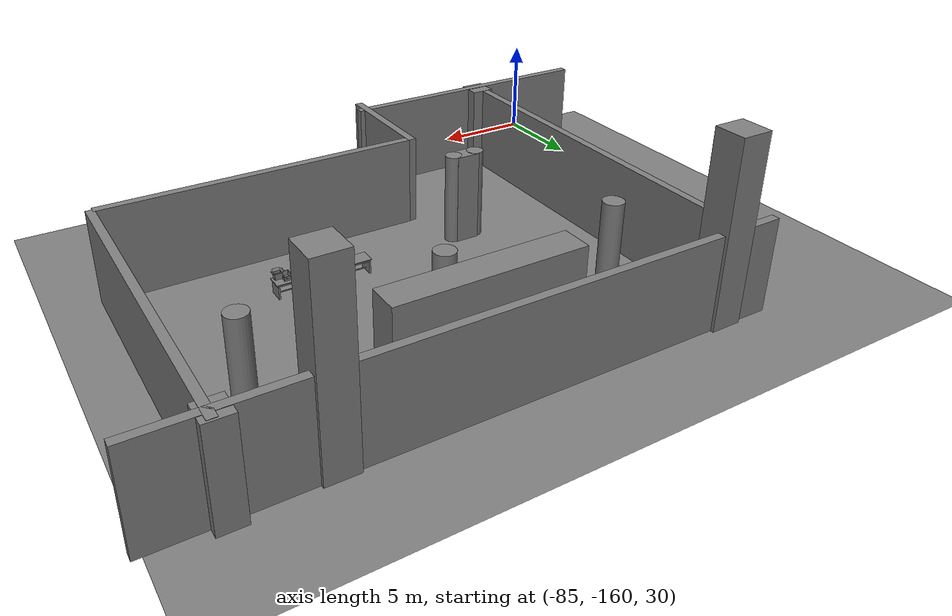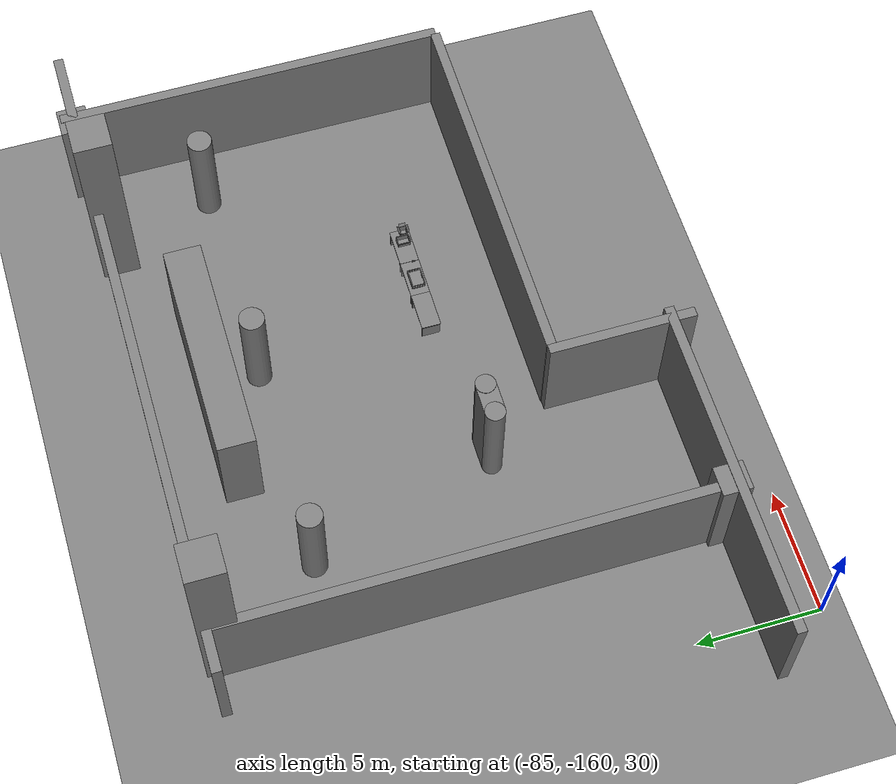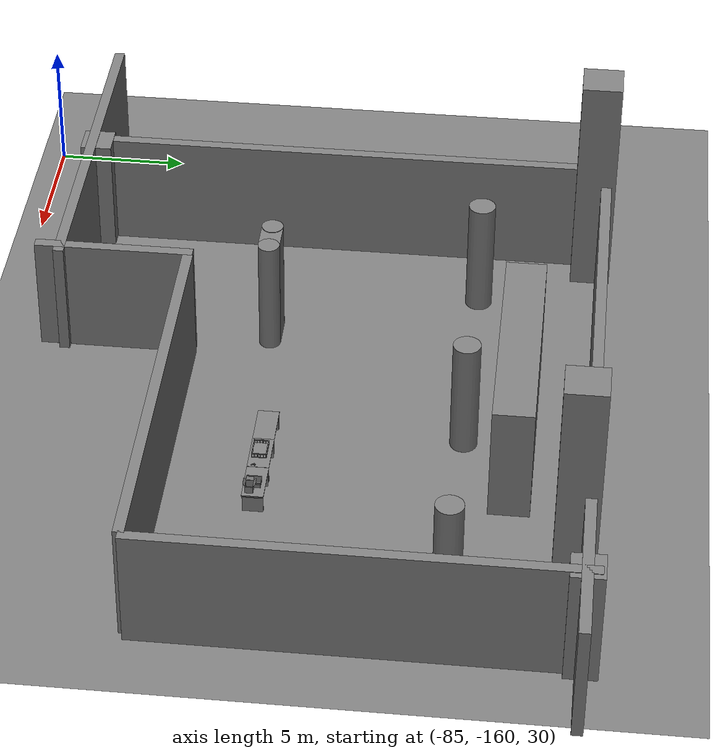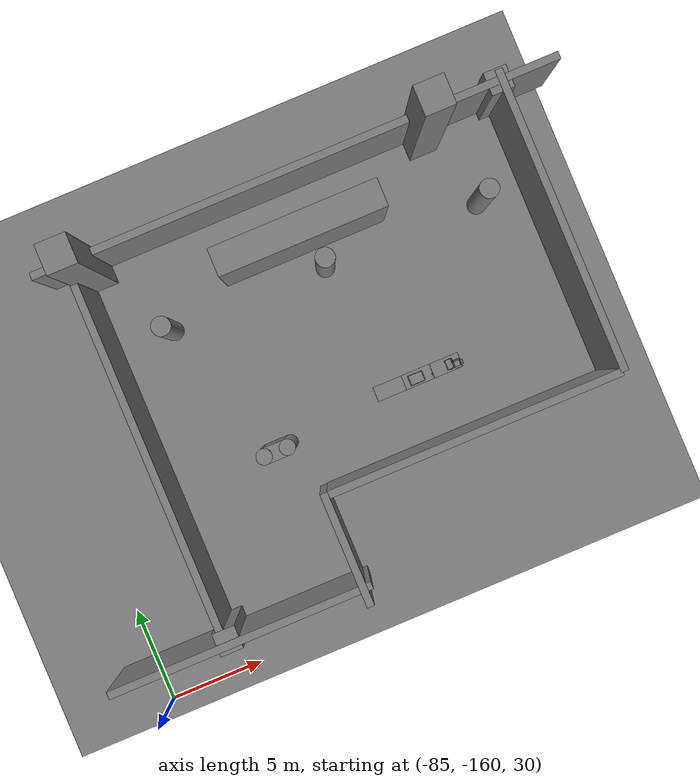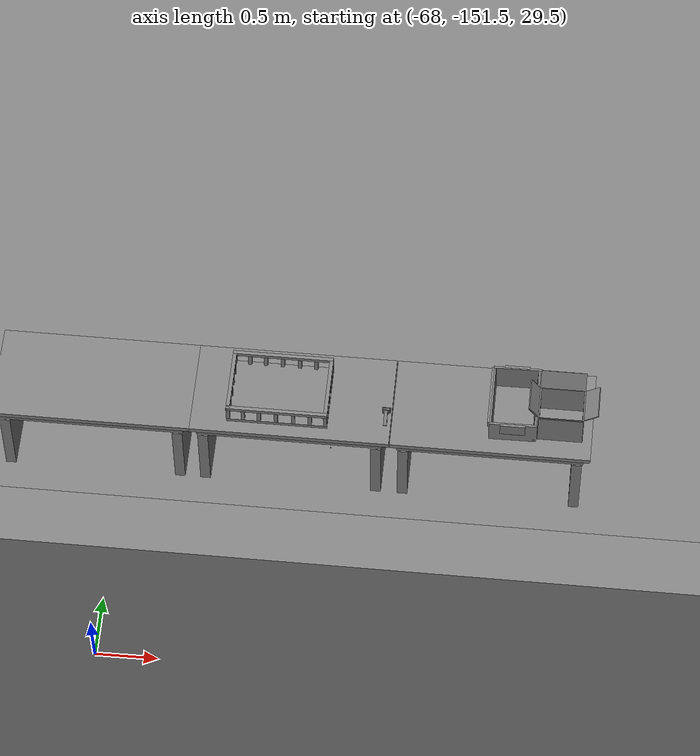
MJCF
<mujoco>
    <option gravity="0.000000000 0.000000000 -9.810000420" timestep="0.0049999999" integrator="implicitfast" density="1.225" viscosity="1.8000001e-05" noslip_iterations="10" iterations="100" sdf_iterations="50">
        <flag multiccd="disable"/>
    </option>
    <size memory="1000M"/>
    <compiler coordinate="local"/>
    <worldbody>
        <light cutoff="30" pos="0 1 1" dir="0 -1 -2"/>
        <light cutoff="30" pos="0 -1 1" dir="0 1 -2"/>
        <body pos="-64.866622925 -149.383972168 30.183746338" euler="89.999992371 89.999946594 0.000000000" name="openloong_gripper_2f85_fix_base_usda_bluebox_01">
            <geom contype="1" conaffinity="1" density="1000" type="box" material="" rgba="0.500000000 0.500000000 0.500000000 1.000000000" solimp="0.899999976 0.949999988 0.001000000" friction="1.000000000 0.005000000 0.000100000" solref="0.020000000 1.000000000" margin="0" condim="3" group="0" pos="0.276596069 0.187225342 0.000061035" quat="0.707107008 0.000077501 0.707106471 0.000077456" size="0.100000001 0.057999998 0.010000000" name="openloong_gripper_2f85_fix_base_usda_geom_0988BF7D_2D14_4F61_ADFD_6B3FEE45395E"/>
            <geom contype="1" conaffinity="1" density="1000" type="box" material="" rgba="0.500000000 0.500000000 0.500000000 1.000000000" solimp="0.899999976 0.949999988 0.001000000" friction="1.000000000 0.005000000 0.000100000" solref="0.020000000 1.000000000" margin="0" condim="3" group="0" pos="0.000000000 0.002883911 0.000000000" quat="1.000000000 0.000000000 0.000000000 0.000000000" size="0.254000008 0.003000000 0.172000006" name="openloong_gripper_2f85_fix_base_usda_geom_9B4032EC_6980_46A0_9546_A42B42260161"/>
            <geom contype="1" conaffinity="1" density="1000" type="box" material="" rgba="0.500000000 0.500000000 0.500000000 1.000000000" solimp="0.899999976 0.949999988 0.001000000" friction="1.000000000 0.005000000 0.000100000" solref="0.020000000 1.000000000" margin="0" condim="3" group="0" pos="0.000015259 0.124874115 0.173477173" quat="0.999796450 0.020176515 -0.000000015 0.000000030" size="0.259999990 0.119999997 0.007000000" name="openloong_gripper_2f85_fix_base_usda_geom_8D1944DF_72EC_467C_8995_F372923078F1"/>
            <geom contype="1" conaffinity="1" density="1000" type="box" material="" rgba="0.500000000 0.500000000 0.500000000 1.000000000" solimp="0.899999976 0.949999988 0.001000000" friction="1.000000000 0.005000000 0.000100000" solref="0.020000000 1.000000000" margin="0" condim="3" group="0" pos="0.000015259 0.124874115 -0.173477173" quat="0.999796450 -0.020176545 -0.000000015 0.000000000" size="0.259999990 0.119999997 0.007000000" name="openloong_gripper_2f85_fix_base_usda_geom_BFFE77CA_F32E_4E04_997F_0D9E2F05C4D8"/>
            <geom contype="1" conaffinity="1" density="1000" type="box" material="" rgba="0.500000000 0.500000000 0.500000000 1.000000000" solimp="0.899999976 0.949999988 0.001000000" friction="1.000000000 0.005000000 0.000100000" solref="0.020000000 1.000000000" margin="0" condim="3" group="0" pos="0.000015259 0.214012146 0.188980103" quat="0.999913096 0.013176724 0.000000015 0.000000000" size="0.259999990 0.029999999 0.012500000" name="openloong_gripper_2f85_fix_base_usda_geom_E4DC3C54_6369_4F69_A437_D56B01D2D31A"/>
            <geom contype="1" conaffinity="1" density="1000" type="box" material="" rgba="0.500000000 0.500000000 0.500000000 1.000000000" solimp="0.899999976 0.949999988 0.001000000" friction="1.000000000 0.005000000 0.000100000" solref="0.020000000 1.000000000" margin="0" condim="3" group="0" pos="-0.258346558 0.125289917 0.001876831" quat="0.702796996 -0.020792052 0.710783184 0.020769238" size="0.189999998 0.119999997 0.009000000" name="openloong_gripper_2f85_fix_base_usda_geom_7B7A1FD7_0C6A_4CB5_9863_34CD2B8C9159"/>
            <geom contype="1" conaffinity="1" density="1000" type="box" material="" rgba="0.500000000 0.500000000 0.500000000 1.000000000" solimp="0.899999976 0.949999988 0.001000000" friction="1.000000000 0.005000000 0.000100000" solref="0.020000000 1.000000000" margin="0" condim="3" group="0" pos="0.000015259 0.214012146 -0.188980103" quat="0.999913096 -0.013176769 0.000000030 0.000000015" size="0.259999990 0.029999999 0.012500000" name="openloong_gripper_2f85_fix_base_usda_geom_D2831EC9_C2BE_4999_9B41_27F5843A24DF"/>
            <geom contype="1" conaffinity="1" density="1000" type="box" material="" rgba="0.500000000 0.500000000 0.500000000 1.000000000" solimp="0.899999976 0.949999988 0.001000000" friction="1.000000000 0.005000000 0.000100000" solref="0.020000000 1.000000000" margin="0" condim="3" group="0" pos="-0.276596069 0.187225342 0.000061035" quat="0.707106650 0.000077441 0.707106709 0.000077456" size="0.100000001 0.057999998 0.010000000" name="openloong_gripper_2f85_fix_base_usda_geom_D42C1B60_C9EB_49F0_A6F6_7727F5815501"/>
            <geom contype="1" conaffinity="1" density="1000" type="box" material="" rgba="0.500000000 0.500000000 0.500000000 1.000000000" solimp="0.899999976 0.949999988 0.001000000" friction="1.000000000 0.005000000 0.000100000" solref="0.020000000 1.000000000" margin="0" condim="3" group="0" pos="0.258346558 0.125289917 0.001876831" quat="0.702851534 0.018856451 0.710823834 -0.019329429" size="0.189999998 0.119999997 0.009000000" name="openloong_gripper_2f85_fix_base_usda_geom_89A603DA_A47E_4D0C_83C4_434837BD8533"/>
            <freejoint name="openloong_gripper_2f85_fix_base_usda_bluebox_01_joint"/>
            <site size="0.005000000 0.005000000 0.005000000" rgba="0.500000000 0.500000000 0.500000000 1.000000000" pos="0.000000000 0.000000000 0.000000000" quat="0.999961913 0.008726534 0.000000000 0.000000000" group="0" type="sphere" name="openloong_gripper_2f85_fix_base_usda_bluebox_01site"/>
        </body>
        <body pos="-64.496299744 -149.491867065 30.235729218" euler="0.000000000 0.000000000 89.999946594" name="openloong_gripper_2f85_fix_base_usda_cardboardbox_01">
            <geom contype="1" conaffinity="1" density="1000" type="box" material="" rgba="0.500000000 0.500000000 0.500000000 1.000000000" solimp="0.899999976 0.949999988 0.001000000" friction="1.000000000 0.005000000 0.000100000" solref="0.020000000 1.000000000" margin="0" condim="3" group="0" pos="-0.003166199 -0.004086494 0.005052090" quat="1.000000000 0.000000000 0.000000000 0.000000000" size="0.142499998 0.177500010 0.005000000" name="openloong_gripper_2f85_fix_base_usda_geom_C339409C_A5C5_4552_A7AE_F80E840A5D5B"/>
            <geom contype="1" conaffinity="1" density="1000" type="box" material="" rgba="0.500000000 0.500000000 0.500000000 1.000000000" solimp="0.899999976 0.949999988 0.001000000" friction="1.000000000 0.005000000 0.000100000" solref="0.020000000 1.000000000" margin="0" condim="3" group="0" pos="-0.003166199 0.170316696 0.150570869" quat="1.000000000 0.000000000 0.000000000 0.000000000" size="0.142499998 0.005000000 0.149999991" name="openloong_gripper_2f85_fix_base_usda_geom_51E608BD_BBC0_4388_A0C2_FCB255315164"/>
            <geom contype="1" conaffinity="1" density="1000" type="box" material="" rgba="0.500000000 0.500000000 0.500000000 1.000000000" solimp="0.899999976 0.949999988 0.001000000" friction="1.000000000 0.005000000 0.000100000" solref="0.020000000 1.000000000" margin="0" condim="3" group="0" pos="-0.147399902 -0.005307198 0.150570869" quat="1.000000000 0.000000000 0.000000000 0.000000000" size="0.005000000 0.177500010 0.149999991" name="openloong_gripper_2f85_fix_base_usda_geom_E3601355_47AB_4145_BA10_3E4D737D5FEC"/>
            <geom contype="1" conaffinity="1" density="1000" type="box" material="" rgba="0.500000000 0.500000000 0.500000000 1.000000000" solimp="0.899999976 0.949999988 0.001000000" friction="1.000000000 0.005000000 0.000100000" solref="0.020000000 1.000000000" margin="0" condim="3" group="0" pos="0.140275955 -0.005307198 0.150570869" quat="1.000000000 0.000000000 0.000000000 0.000000000" size="0.005000000 0.177500010 0.149999991" name="openloong_gripper_2f85_fix_base_usda_geom_BA0BA581_8193_4973_A9E7_83394277BAF9"/>
            <geom contype="1" conaffinity="1" density="1000" type="box" material="" rgba="0.500000000 0.500000000 0.500000000 1.000000000" solimp="0.899999976 0.949999988 0.001000000" friction="1.000000000 0.005000000 0.000100000" solref="0.020000000 1.000000000" margin="0" condim="3" group="0" pos="-0.003166199 -0.181550980 0.150570869" quat="1.000000000 0.000000000 0.000000000 0.000000000" size="0.142499998 0.005000000 0.149999991" name="openloong_gripper_2f85_fix_base_usda_geom_E0596E29_839C_41C8_8095_37DC19BEE055"/>
            <freejoint name="openloong_gripper_2f85_fix_base_usda_cardboardbox_01_joint"/>
            <site size="0.005000000 0.005000000 0.005000000" rgba="0.500000000 0.500000000 0.500000000 1.000000000" pos="0.000000000 0.000000000 0.000000000" quat="0.999961913 0.008726535 0.000000000 0.000000000" group="0" type="sphere" name="openloong_gripper_2f85_fix_base_usda_site_1D90DA2E_7D50_42E3_ACAF_AC15B2C24687"/>
            <body pos="0.139160156 -0.004048347 0.301930904" euler="-179.999954224 49.383502960 179.999954224" name="openloong_gripper_2f85_fix_base_usda_A1_006">
                <geom contype="1" conaffinity="1" density="1000" type="box" material="" rgba="0.500000000 0.500000000 0.500000000 1.000000000" solimp="0.899999976 0.949999988 0.001000000" friction="1.000000000 0.005000000 0.000100000" solref="0.020000000 1.000000000" margin="0" condim="3" group="0" pos="-0.071587563 0.000009537 0.001745224" quat="0.999999881 0.000000000 0.000000000 0.000000000" size="0.071249999 0.179999992 0.002500000" name="openloong_gripper_2f85_fix_base_usda_geom_7E4DF919_8AD0_415D_B95D_F7F216855FA7"/>
                <joint armature="0" stiffness="0.07" damping="0.0099999998" axis="0.000000 1.000000 0.000000" type="hinge" name="openloong_gripper_2f85_fix_base_usda_A1_006"/>
            </body>
            <body pos="-0.145902634 -0.004086494 0.301938057" euler="-180.000000000 -60.000011444 -180.000000000" name="openloong_gripper_2f85_fix_base_usda_A2_006">
                <geom contype="1" conaffinity="1" density="1000" type="box" material="" rgba="0.500000000 0.500000000 0.500000000 1.000000000" solimp="0.899999976 0.949999988 0.001000000" friction="1.000000000 0.005000000 0.000100000" solref="0.020000000 1.000000000" margin="0" condim="3" group="0" pos="0.071268082 0.000009537 0.002717972" quat="0.000002921 0.000000000 -0.000000030 0.999999881" size="0.071249999 0.179999992 0.002500000" name="openloong_gripper_2f85_fix_base_usda_geom_10E46E1F_90D0_4CC2_B353_3BC1C759E324"/>
                <joint armature="0" stiffness="0.07" damping="0.0099999998" axis="0.000000 1.000000 0.000000" type="hinge" name="openloong_gripper_2f85_fix_base_usda_A2_006"/>
            </body>
            <body pos="-0.003385544 0.175991058 0.301930904" euler="-125.858116150 -0.000004561 0.000002331" name="openloong_gripper_2f85_fix_base_usda_B2_006">
                <geom contype="1" conaffinity="1" density="1000" type="box" material="" rgba="0.500000000 0.500000000 0.500000000 1.000000000" solimp="0.899999976 0.949999988 0.001000000" friction="1.000000000 0.005000000 0.000100000" solref="0.020000000 1.000000000" margin="0" condim="3" group="0" pos="0.000009537 -0.070939064 -0.002470016" quat="0.999614120 0.027776197 -0.000000015 0.000000030" size="0.137500003 0.064999998 0.005000000" name="openloong_gripper_2f85_fix_base_usda_geom_2DB238D2_1352_4219_81D1_5D9F9B87C0DE"/>
                <joint armature="0" stiffness="0.07" damping="0.0099999998" axis="1.000000 0.000000 0.000000" type="hinge" name="openloong_gripper_2f85_fix_base_usda_B2_006"/>
            </body>
            <body pos="-0.003385544 -0.184140205 0.301938057" euler="147.805557251 0.000000000 0.000000000" name="openloong_gripper_2f85_fix_base_usda_B1_006">
                <geom contype="1" conaffinity="1" density="1000" type="box" material="" rgba="0.500000000 0.500000000 0.500000000 1.000000000" solimp="0.899999976 0.949999988 0.001000000" friction="1.000000000 0.005000000 0.000100000" solref="0.020000000 1.000000000" margin="0" condim="3" group="0" pos="-0.000028610 0.070202351 -0.002703667" quat="0.999614179 -0.027776167 0.000000000 0.000000000" size="0.137500003 0.064999998 0.005000000" name="openloong_gripper_2f85_fix_base_usda_geom_07CB87E6_280F_4447_96C4_3CC6A873FC26"/>
                <joint armature="0" stiffness="0.07" damping="0.0099999998" axis="1.000000 0.000000 0.000000" type="hinge" name="openloong_gripper_2f85_fix_base_usda_B1_006"/>
            </body>
        </body>
        <body pos="-65.882858276 -149.481979370 30.229999542" euler="-64.487716675 0.000000000 0.000000000" name="openloong_gripper_2f85_fix_base_usda_Barcode">
            <geom contype="1" conaffinity="1" density="1000" type="box" material="" rgba="0.500000000 0.500000000 0.500000000 1.000000000" solimp="0.899999976 0.949999988 0.001000000" friction="1.000000000 0.005000000 0.000100000" solref="0.020000000 1.000000000" margin="0" condim="3" group="0" pos="0.000000000 0.013038635 0.001419067" quat="0.000000000 0.000000000 0.000000000 1.000000119" size="0.034000002 0.010000000 0.017999999" name="openloong_gripper_2f85_fix_base_usda_geom_B86DB480_4E60_48B3_870C_9BD8F5E7D808"/>
            <geom contype="1" conaffinity="1" density="1000" type="box" material="" rgba="0.500000000 0.500000000 0.500000000 1.000000000" solimp="0.899999976 0.949999988 0.001000000" friction="1.000000000 0.005000000 0.000100000" solref="0.020000000 1.000000000" margin="0" condim="3" group="0" pos="0.000000000 -0.035301208 -0.007095337" quat="0.000000000 0.000000000 -0.043619365 0.999048233" size="0.028999999 0.010000000 0.020000000" name="openloong_gripper_2f85_fix_base_usda_geom_2ED359A9_274D_41D9_95EB_1B7D4864CB77"/>
            <geom contype="1" conaffinity="1" density="1000" type="box" material="" rgba="0.500000000 0.500000000 0.500000000 1.000000000" solimp="0.899999976 0.949999988 0.001000000" friction="1.000000000 0.005000000 0.000100000" solref="0.020000000 1.000000000" margin="0" condim="3" group="0" pos="0.000000000 -0.043411255 -0.011749268" quat="0.922262907 0.386563420 0.000000000 0.000000000" size="0.026000001 0.010000000 0.020000000" name="openloong_gripper_2f85_fix_base_usda_geom_49253FFD_2918_478D_A317_718CA0951801"/>
            <geom contype="1" conaffinity="1" density="1000" type="box" material="" rgba="0.500000000 0.500000000 0.500000000 1.000000000" solimp="0.899999976 0.949999988 0.001000000" friction="1.000000000 0.005000000 0.000100000" solref="0.020000000 1.000000000" margin="0" condim="3" group="0" pos="0.000000000 -0.016967773 -0.031860352" quat="0.000000000 0.000000000 0.000000000 1.000000119" size="0.008000000 0.010000000 0.013000000" name="openloong_gripper_2f85_fix_base_usda_geom_9DF1E7CA_2837_42C7_920F_B9DD840AC3D9"/>
            <geom contype="1" conaffinity="1" density="1000" type="box" material="" rgba="0.500000000 0.500000000 0.500000000 1.000000000" solimp="0.899999976 0.949999988 0.001000000" friction="1.000000000 0.005000000 0.000100000" solref="0.020000000 1.000000000" margin="0" condim="3" group="0" pos="0.000000000 -0.001869202 0.000312805" quat="0.953716993 0.300705761 0.000000000 0.000000000" size="0.032000002 0.010000000 0.018999999" name="openloong_gripper_2f85_fix_base_usda_geom_BF14C255_FC9E_4D1C_B8D2_E34563F2BFD9"/>
            <geom contype="1" conaffinity="1" density="1000" type="box" material="" rgba="0.500000000 0.500000000 0.500000000 1.000000000" solimp="0.899999976 0.949999988 0.001000000" friction="1.000000000 0.005000000 0.000100000" solref="0.020000000 1.000000000" margin="0" condim="3" group="0" pos="0.000000000 -0.019531250 -0.003173828" quat="0.953716993 0.300705761 0.000000000 0.000000000" size="0.030999999 0.010000000 0.020000000" name="openloong_gripper_2f85_fix_base_usda_geom_5E7824F3_D1BE_4531_A4BA_AABC93D7106B"/>
            <geom contype="1" conaffinity="1" density="1000" type="box" material="" rgba="0.500000000 0.500000000 0.500000000 1.000000000" solimp="0.899999976 0.949999988 0.001000000" friction="1.000000000 0.005000000 0.000100000" solref="0.020000000 1.000000000" margin="0" condim="3" group="0" pos="0.000000000 -0.035301208 -0.007095337" quat="0.953716993 0.300705761 0.000000000 0.000000000" size="0.028999999 0.010000000 0.020000000" name="openloong_gripper_2f85_fix_base_usda_geom_E320D3B6_1363_4BC9_A317_24C7786391FB"/>
            <geom contype="1" conaffinity="1" density="1000" type="box" material="" rgba="0.500000000 0.500000000 0.500000000 1.000000000" solimp="0.899999976 0.949999988 0.001000000" friction="1.000000000 0.005000000 0.000100000" solref="0.020000000 1.000000000" margin="0" condim="3" group="0" pos="0.000000000 -0.042617798 -0.071121216" quat="0.000000000 0.000000000 0.000000000 1.000000119" size="0.013000000 0.021000000 0.059999999" name="openloong_gripper_2f85_fix_base_usda_geom_6EB347FD_3FB0_4E1C_B180_ECEC60BCDFA4"/>
            <freejoint name="openloong_gripper_2f85_fix_base_usda_Barcode_joint"/>
            <site size="0.005000000 0.005000000 0.005000000" rgba="0.500000000 0.500000000 0.500000000 1.000000000" pos="0.000000000 0.000000000 0.000000000" quat="1.000000000 0.000000000 0.000000000 0.000000000" group="0" type="sphere" name="openloong_gripper_2f85_fix_base_usda_Barcode_site"/>
        </body>
        <body pos="-66.745018005 -149.392349243 30.184000015" euler="0.000000000 0.000000000 89.999946594" name="[22329623915371]_Basket_01">
            <geom contype="1" conaffinity="1" density="1000" type="box" material="" rgba="0.500000000 0.500000000 0.500000000 1.000000000" solimp="0.899999976 0.949999988 0.001000000" friction="1.000000000 0.005000000 0.000100000" solref="0.020000000 1.000000000" margin="0" condim="3" group="0" pos="-0.052425385 0.389207840 0.089787483" quat="0.707107008 0.000000000 0.000000000 0.707106411" size="0.014249999 0.014249999 0.059999999" name="[22329623915371]_geom_4FCC7DE2_C9E0_40D2_B9D7_39D74CBD8FF8"/>
            <geom contype="1" conaffinity="1" density="1000" type="box" material="" rgba="0.500000000 0.500000000 0.500000000 1.000000000" solimp="0.899999976 0.949999988 0.001000000" friction="1.000000000 0.005000000 0.000100000" solref="0.020000000 1.000000000" margin="0" condim="3" group="0" pos="0.264015198 -0.133043289 0.089787483" quat="0.707107008 0.000000000 0.000000000 0.707106411" size="0.014249999 0.014249999 0.059999999" name="[22329623915371]_geom_2ED4B00D_FF50_4BC2_B9E9_0AF4A605B77F"/>
            <geom contype="1" conaffinity="1" density="1000" type="box" material="" rgba="0.500000000 0.500000000 0.500000000 1.000000000" solimp="0.899999976 0.949999988 0.001000000" friction="1.000000000 0.005000000 0.000100000" solref="0.020000000 1.000000000" margin="0" condim="3" group="0" pos="-0.264015198 -0.265548706 0.089793205" quat="0.707107008 0.000000000 0.000000000 0.707106411" size="0.014249999 0.014249999 0.059999999" name="[22329623915371]_geom_D2E86D8D_8D8E_4E5C_BF1D_40A0D597A59E"/>
            <geom contype="1" conaffinity="1" density="1000" type="box" material="" rgba="0.500000000 0.500000000 0.500000000 1.000000000" solimp="0.899999976 0.949999988 0.001000000" friction="1.000000000 0.005000000 0.000100000" solref="0.020000000 1.000000000" margin="0" condim="3" group="0" pos="-0.160263062 -0.389322281 0.089793205" quat="0.707107008 0.000000000 0.000000000 0.707106411" size="0.014249999 0.014249999 0.059999999" name="[22329623915371]_geom_EEC620C1_338B_4BCF_88F3_11958CB2068D"/>
            <geom contype="1" conaffinity="1" density="1000" type="box" material="" rgba="0.500000000 0.500000000 0.500000000 1.000000000" solimp="0.899999976 0.949999988 0.001000000" friction="1.000000000 0.005000000 0.000100000" solref="0.020000000 1.000000000" margin="0" condim="3" group="0" pos="0.162265778 -0.389322281 0.089787483" quat="0.707107008 0.000000000 0.000000000 0.707106411" size="0.014249999 0.014249999 0.059999999" name="[22329623915371]_geom_1083F7F6_6504_4AA3_9EA4_BA68027CB9D7"/>
            <geom contype="1" conaffinity="1" density="1000" type="box" material="" rgba="0.500000000 0.500000000 0.500000000 1.000000000" solimp="0.899999976 0.949999988 0.001000000" friction="1.000000000 0.005000000 0.000100000" solref="0.020000000 1.000000000" margin="0" condim="3" group="0" pos="0.264015198 0.389207840 0.089787483" quat="0.707107008 0.000000000 0.000000000 0.707106411" size="0.014249999 0.014249999 0.059999999" name="[22329623915371]_geom_B2D1C2F4_9FB1_4585_98A0_2921687EBC3B"/>
            <geom contype="1" conaffinity="1" density="1000" type="box" material="" rgba="0.500000000 0.500000000 0.500000000 1.000000000" solimp="0.899999976 0.949999988 0.001000000" friction="1.000000000 0.005000000 0.000100000" solref="0.020000000 1.000000000" margin="0" condim="3" group="0" pos="-0.264015198 -0.133043289 0.089793205" quat="0.707107008 0.000000000 0.000000000 0.707106411" size="0.014249999 0.014249999 0.059999999" name="[22329623915371]_geom_AF40C207_60AA_4DAF_BEE8_4F2F3DBA7851"/>
            <geom contype="1" conaffinity="1" density="1000" type="box" material="" rgba="0.500000000 0.500000000 0.500000000 1.000000000" solimp="0.899999976 0.949999988 0.001000000" friction="1.000000000 0.005000000 0.000100000" solref="0.020000000 1.000000000" margin="0" condim="3" group="0" pos="-0.264026642 0.269256592 0.089793205" quat="0.707107008 0.000000000 0.000000000 0.707106411" size="0.014249999 0.014249999 0.059999999" name="[22329623915371]_geom_FA979606_8BF1_4F6E_8F02_DC4AA704944A"/>
            <geom contype="1" conaffinity="1" density="1000" type="box" material="" rgba="0.500000000 0.500000000 0.500000000 1.000000000" solimp="0.899999976 0.949999988 0.001000000" friction="1.000000000 0.005000000 0.000100000" solref="0.020000000 1.000000000" margin="0" condim="3" group="0" pos="0.054462433 0.389207840 0.089787483" quat="0.707107008 0.000000000 0.000000000 0.707106411" size="0.014249999 0.014249999 0.059999999" name="[22329623915371]_geom_3AEEA14C_8927_404C_8700_111902E17DE2"/>
            <geom contype="1" conaffinity="1" density="1000" type="box" material="" rgba="0.500000000 0.500000000 0.500000000 1.000000000" solimp="0.899999976 0.949999988 0.001000000" friction="1.000000000 0.005000000 0.000100000" solref="0.020000000 1.000000000" margin="0" condim="3" group="0" pos="0.054462433 -0.389322281 0.089787483" quat="0.707107008 0.000000000 0.000000000 0.707106411" size="0.014249999 0.014249999 0.059999999" name="[22329623915371]_geom_8E9F27FA_DA8C_4D63_94B3_8E648AFFB5E2"/>
            <geom contype="1" conaffinity="1" density="1000" type="box" material="" rgba="0.500000000 0.500000000 0.500000000 1.000000000" solimp="0.899999976 0.949999988 0.001000000" friction="1.000000000 0.005000000 0.000100000" solref="0.020000000 1.000000000" margin="0" condim="3" group="0" pos="0.264015198 0.269256592 0.089793205" quat="0.707107008 0.000000000 0.000000000 0.707106411" size="0.014249999 0.014249999 0.059999999" name="[22329623915371]_geom_02F740B6_7528_435F_984F_7F7858732842"/>
            <geom contype="1" conaffinity="1" density="1000" type="box" material="" rgba="0.500000000 0.500000000 0.500000000 1.000000000" solimp="0.899999976 0.949999988 0.001000000" friction="1.000000000 0.005000000 0.000100000" solref="0.020000000 1.000000000" margin="0" condim="3" group="0" pos="0.264015198 -0.389322281 0.089787483" quat="0.707107008 0.000000000 0.000000000 0.707106411" size="0.014249999 0.014249999 0.059999999" name="[22329623915371]_geom_E316BAE4_124A_4CD9_8FAE_EE77C9EA85AE"/>
            <geom contype="1" conaffinity="1" density="1000" type="box" material="" rgba="0.500000000 0.500000000 0.500000000 1.000000000" solimp="0.899999976 0.949999988 0.001000000" friction="1.000000000 0.005000000 0.000100000" solref="0.020000000 1.000000000" margin="0" condim="3" group="0" pos="0.000000000 0.000000000 0.015998840" quat="0.707107008 0.000000000 0.000000000 0.707106411" size="0.403499991 0.279000014 0.015750000" name="[22329623915371]_geom_B67F4EAB_22C1_42F6_8DEF_BE09E21B1718"/>
            <geom contype="1" conaffinity="1" density="1000" type="box" material="" rgba="0.500000000 0.500000000 0.500000000 1.000000000" solimp="0.899999976 0.949999988 0.001000000" friction="1.000000000 0.005000000 0.000100000" solref="0.020000000 1.000000000" margin="0" condim="3" group="0" pos="0.000000000 -0.389476776 0.163619041" quat="0.707107008 0.000000000 0.000000000 0.707106411" size="0.015000000 0.277500004 0.015750000" name="[22329623915371]_geom_08E45AEC_D690_4E70_AA96_B81920532E5B"/>
            <geom contype="1" conaffinity="1" density="1000" type="box" material="" rgba="0.500000000 0.500000000 0.500000000 1.000000000" solimp="0.899999976 0.949999988 0.001000000" friction="1.000000000 0.005000000 0.000100000" solref="0.020000000 1.000000000" margin="0" condim="3" group="0" pos="0.162265778 0.389207840 0.089787483" quat="0.707107008 0.000000000 0.000000000 0.707106411" size="0.014249999 0.014249999 0.059999999" name="[22329623915371]_geom_A5FC0AE2_553E_419D_9042_492E3A4DFC27"/>
            <geom contype="1" conaffinity="1" density="1000" type="box" material="" rgba="0.500000000 0.500000000 0.500000000 1.000000000" solimp="0.899999976 0.949999988 0.001000000" friction="1.000000000 0.005000000 0.000100000" solref="0.020000000 1.000000000" margin="0" condim="3" group="0" pos="0.000000000 0.389471054 0.163619041" quat="0.707107008 0.000000000 0.000000000 0.707106411" size="0.015000000 0.277500004 0.015750000" name="[22329623915371]_geom_1BF5D99C_EFC5_464F_B567_D5AA4B319743"/>
            <geom contype="1" conaffinity="1" density="1000" type="box" material="" rgba="0.500000000 0.500000000 0.500000000 1.000000000" solimp="0.899999976 0.949999988 0.001000000" friction="1.000000000 0.005000000 0.000100000" solref="0.020000000 1.000000000" margin="0" condim="3" group="0" pos="-0.263511658 0.000000000 0.163619041" quat="0.707107008 0.000000000 0.000000000 0.707106411" size="0.403499991 0.015000000 0.015750000" name="[22329623915371]_geom_55F5C58B_3159_41DB_A9E5_BD46E518994B"/>
            <geom contype="1" conaffinity="1" density="1000" type="box" material="" rgba="0.500000000 0.500000000 0.500000000 1.000000000" solimp="0.899999976 0.949999988 0.001000000" friction="1.000000000 0.005000000 0.000100000" solref="0.020000000 1.000000000" margin="0" condim="3" group="0" pos="-0.264015198 0.141334534 0.089793205" quat="0.707107008 0.000000000 0.000000000 0.707106411" size="0.014249999 0.014249999 0.059999999" name="[22329623915371]_geom_3B41FEE4_7791_465D_879B_91DFC4D03C8E"/>
            <geom contype="1" conaffinity="1" density="1000" type="box" material="" rgba="0.500000000 0.500000000 0.500000000 1.000000000" solimp="0.899999976 0.949999988 0.001000000" friction="1.000000000 0.005000000 0.000100000" solref="0.020000000 1.000000000" margin="0" condim="3" group="0" pos="0.264015198 -0.265548706 0.089787483" quat="0.707107008 0.000000000 0.000000000 0.707106411" size="0.014249999 0.014249999 0.059999999" name="[22329623915371]_geom_DF45ED4F_B543_4A11_83F9_457DBB6C98C8"/>
            <geom contype="1" conaffinity="1" density="1000" type="box" material="" rgba="0.500000000 0.500000000 0.500000000 1.000000000" solimp="0.899999976 0.949999988 0.001000000" friction="1.000000000 0.005000000 0.000100000" solref="0.020000000 1.000000000" margin="0" condim="3" group="0" pos="-0.160263062 0.389207840 0.089787483" quat="0.707107008 0.000000000 0.000000000 0.707106411" size="0.014249999 0.014249999 0.059999999" name="[22329623915371]_geom_9F4B37AD_7653_4A67_9919_15F08E7BB30B"/>
            <geom contype="1" conaffinity="1" density="1000" type="box" material="" rgba="0.500000000 0.500000000 0.500000000 1.000000000" solimp="0.899999976 0.949999988 0.001000000" friction="1.000000000 0.005000000 0.000100000" solref="0.020000000 1.000000000" margin="0" condim="3" group="0" pos="-0.052425385 -0.389322281 0.089787483" quat="0.707107008 0.000000000 0.000000000 0.707106411" size="0.014249999 0.014249999 0.059999999" name="[22329623915371]_geom_51190849_0AA5_40B3_863F_AE1693CC80D0"/>
            <geom contype="1" conaffinity="1" density="1000" type="box" material="" rgba="0.500000000 0.500000000 0.500000000 1.000000000" solimp="0.899999976 0.949999988 0.001000000" friction="1.000000000 0.005000000 0.000100000" solref="0.020000000 1.000000000" margin="0" condim="3" group="0" pos="-0.264026642 -0.389322281 0.089793205" quat="0.707107008 0.000000000 0.000000000 0.707106411" size="0.014249999 0.014249999 0.059999999" name="[22329623915371]_geom_EE588505_08D9_4D76_9997_0FB18553AF80"/>
            <geom contype="1" conaffinity="1" density="1000" type="box" material="" rgba="0.500000000 0.500000000 0.500000000 1.000000000" solimp="0.899999976 0.949999988 0.001000000" friction="1.000000000 0.005000000 0.000100000" solref="0.020000000 1.000000000" margin="0" condim="3" group="0" pos="0.264015198 0.141334534 0.089787483" quat="0.707107008 0.000000000 0.000000000 0.707106411" size="0.014249999 0.014249999 0.059999999" name="[22329623915371]_geom_0D5BB854_9926_4AA9_8EFB_F9CDEDF25596"/>
            <geom contype="1" conaffinity="1" density="1000" type="box" material="" rgba="0.500000000 0.500000000 0.500000000 1.000000000" solimp="0.899999976 0.949999988 0.001000000" friction="1.000000000 0.005000000 0.000100000" solref="0.020000000 1.000000000" margin="0" condim="3" group="0" pos="-0.264015198 0.389207840 0.089793205" quat="0.707107008 0.000000000 0.000000000 0.707106411" size="0.014249999 0.014249999 0.059999999" name="[22329623915371]_geom_256856EA_F705_423D_B1D5_30C47CA4AC8B"/>
            <geom contype="1" conaffinity="1" density="1000" type="box" material="" rgba="0.500000000 0.500000000 0.500000000 1.000000000" solimp="0.899999976 0.949999988 0.001000000" friction="1.000000000 0.005000000 0.000100000" solref="0.020000000 1.000000000" margin="0" condim="3" group="0" pos="0.264015198 0.004480362 0.089787483" quat="0.707107008 0.000000000 0.000000000 0.707106411" size="0.014249999 0.014249999 0.059999999" name="[22329623915371]_geom_DB63B3B6_3554_480A_8C7A_20FB7056B0C0"/>
            <geom contype="1" conaffinity="1" density="1000" type="box" material="" rgba="0.500000000 0.500000000 0.500000000 1.000000000" solimp="0.899999976 0.949999988 0.001000000" friction="1.000000000 0.005000000 0.000100000" solref="0.020000000 1.000000000" margin="0" condim="3" group="0" pos="0.263694763 -0.000011444 0.163619041" quat="0.707107008 0.000000000 0.000000000 0.707106411" size="0.403499991 0.015000000 0.015750000" name="[22329623915371]_geom_8333D9ED_B38E_4FB3_9A34_5C1ABFC87B6B"/>
            <geom contype="1" conaffinity="1" density="1000" type="box" material="" rgba="0.500000000 0.500000000 0.500000000 1.000000000" solimp="0.899999976 0.949999988 0.001000000" friction="1.000000000 0.005000000 0.000100000" solref="0.020000000 1.000000000" margin="0" condim="3" group="0" pos="-0.264015198 0.004480362 0.089793205" quat="0.707107008 0.000000000 0.000000000 0.707106411" size="0.014249999 0.014249999 0.059999999" name="[22329623915371]_geom_13C98854_3BB8_4B3D_93F7_181A7ABC652C"/>
            <freejoint name="[22329623915371]_joint_B60ED450_A238_4B52_AE5E_FF03C0CBE8C9"/>
        </body>
        <body pos="0.000000000 0.000000000 0.000000000" euler="0.000000000 0.000000000 0.000000000" name="Static Objects_Static Objects">
            <geom contype="1" conaffinity="1" density="1000" type="box" material="" rgba="0.500000000 0.500000000 0.500000000 1.000000000" solimp="0.899999976 0.949999988 0.001000000" friction="1.000000000 0.005000000 0.000100000" solref="0.020000000 1.000000000" margin="0" condim="3" group="0" pos="-67.544113159 -149.365814209 29.727830887" quat="0.500000417 0.499999970 0.499999553 0.499999970" size="0.381000012 0.319999993 0.041000001" name="Static Objects_geom_63D09439_6A5C_4686_9534_4F2797BF59D4"/>
            <geom contype="1" conaffinity="1" density="1000" type="box" material="" rgba="0.500000000 0.500000000 0.500000000 1.000000000" solimp="0.899999976 0.949999988 0.001000000" friction="1.000000000 0.005000000 0.000100000" solref="0.020000000 1.000000000" margin="0" condim="3" group="0" pos="-68.239501953 -149.365814209 30.086868286" quat="0.500000417 0.499999970 0.499999553 0.499999970" size="0.370999992 0.039500002 0.745000005" name="Static Objects_geom_C3E48D4E_DAD5_4BD8_BF07_45597B49FA1A"/>
            <geom contype="1" conaffinity="1" density="1000" type="box" material="" rgba="0.500000000 0.500000000 0.500000000 1.000000000" solimp="0.899999976 0.949999988 0.001000000" friction="1.000000000 0.005000000 0.000100000" solref="0.020000000 1.000000000" margin="0" condim="3" group="0" pos="-68.239501953 -149.365814209 30.147235870" quat="0.500000417 0.499999970 0.499999553 0.499999970" size="0.400000006 0.022000000 0.800000012" name="Static Objects_geom_5A9A6F4F_ADB2_4FF1_AF04_F2FF785F5AEC"/>
            <geom contype="1" conaffinity="1" density="1000" type="box" material="" rgba="0.500000000 0.500000000 0.500000000 1.000000000" solimp="0.899999976 0.949999988 0.001000000" friction="1.000000000 0.005000000 0.000100000" solref="0.020000000 1.000000000" margin="0" condim="3" group="0" pos="-68.934890747 -149.365814209 29.727830887" quat="0.500000417 0.499999970 0.499999553 0.499999970" size="0.381000012 0.319999993 0.041000001" name="Static Objects_geom_68B229AD_14DD_4F2D_B74B_3970B6C9D5DC"/>
            <geom contype="1" conaffinity="1" density="1000" type="box" material="" rgba="0.500000000 0.500000000 0.500000000 1.000000000" solimp="0.899999976 0.949999988 0.001000000" friction="1.000000000 0.005000000 0.000100000" solref="0.020000000 1.000000000" margin="0" condim="3" group="0" pos="-68.239501953 -149.365814209 29.561563492" quat="0.500000417 0.499999970 0.499999553 0.499999970" size="0.020000000 0.022000000 0.660000026" name="Static Objects_geom_E7B50EF5_C954_41B8_B637_6BD412D1B461"/>
            <geom contype="1" conaffinity="1" density="1000" type="box" material="" rgba="0.500000000 0.500000000 0.500000000 1.000000000" solimp="0.899999976 0.949999988 0.001000000" friction="1.000000000 0.005000000 0.000100000" solref="0.020000000 1.000000000" margin="0" condim="3" group="0" pos="-65.945671082 -149.365814209 29.727830887" quat="0.500000417 0.499999970 0.499999553 0.499999970" size="0.381000012 0.319999993 0.041000001" name="Static Objects_geom_F6964B7F_3073_4B40_84E5_42D8252B9D03"/>
            <geom contype="1" conaffinity="1" density="1000" type="box" material="" rgba="0.500000000 0.500000000 0.500000000 1.000000000" solimp="0.899999976 0.949999988 0.001000000" friction="1.000000000 0.005000000 0.000100000" solref="0.020000000 1.000000000" margin="0" condim="3" group="0" pos="-66.641059875 -149.365814209 30.086868286" quat="0.500000417 0.499999970 0.499999553 0.499999970" size="0.370999992 0.039500002 0.745000005" name="Static Objects_geom_AC616375_CD8E_44CE_B35E_BC387577A88A"/>
            <geom contype="1" conaffinity="1" density="1000" type="box" material="" rgba="0.500000000 0.500000000 0.500000000 1.000000000" solimp="0.899999976 0.949999988 0.001000000" friction="1.000000000 0.005000000 0.000100000" solref="0.020000000 1.000000000" margin="0" condim="3" group="0" pos="-66.641059875 -149.365814209 30.147235870" quat="0.500000417 0.499999970 0.499999553 0.499999970" size="0.400000006 0.022000000 0.800000012" name="Static Objects_geom_2B91EE96_D288_440B_BA23_6B0E9918274F"/>
            <geom contype="1" conaffinity="1" density="1000" type="box" material="" rgba="0.500000000 0.500000000 0.500000000 1.000000000" solimp="0.899999976 0.949999988 0.001000000" friction="1.000000000 0.005000000 0.000100000" solref="0.020000000 1.000000000" margin="0" condim="3" group="0" pos="-67.336448669 -149.365814209 29.727830887" quat="0.500000417 0.499999970 0.499999553 0.499999970" size="0.381000012 0.319999993 0.041000001" name="Static Objects_geom_CAAE42AB_1B72_45FD_9963_C6F8E4D4469F"/>
            <geom contype="1" conaffinity="1" density="1000" type="box" material="" rgba="0.500000000 0.500000000 0.500000000 1.000000000" solimp="0.899999976 0.949999988 0.001000000" friction="1.000000000 0.005000000 0.000100000" solref="0.020000000 1.000000000" margin="0" condim="3" group="0" pos="-66.641059875 -149.365814209 29.561563492" quat="0.500000417 0.499999970 0.499999553 0.499999970" size="0.020000000 0.022000000 0.660000026" name="Static Objects_geom_11A23265_5E60_4020_B72E_F9C20061C1F2"/>
            <geom contype="1" conaffinity="1" density="1000" type="box" material="" rgba="0.500000000 0.500000000 0.500000000 1.000000000" solimp="0.899999976 0.949999988 0.001000000" friction="1.000000000 0.005000000 0.000100000" solref="0.020000000 1.000000000" margin="0" condim="3" group="0" pos="-64.338577271 -149.365814209 29.727830887" quat="0.500000417 0.499999970 0.499999553 0.499999970" size="0.381000012 0.319999993 0.041000001" name="Static Objects_geom_CBF3912C_C16D_4D5E_9EBB_8E62807F2293"/>
            <geom contype="1" conaffinity="1" density="1000" type="box" material="" rgba="0.500000000 0.500000000 0.500000000 1.000000000" solimp="0.899999976 0.949999988 0.001000000" friction="1.000000000 0.005000000 0.000100000" solref="0.020000000 1.000000000" margin="0" condim="3" group="0" pos="-65.033966064 -149.365814209 30.086868286" quat="0.500000417 0.499999970 0.499999553 0.499999970" size="0.370999992 0.039500002 0.745000005" name="Static Objects_geom_74EE4F26_9F76_44D9_8716_8D797BE4101D"/>
            <geom contype="1" conaffinity="1" density="1000" type="box" material="" rgba="0.500000000 0.500000000 0.500000000 1.000000000" solimp="0.899999976 0.949999988 0.001000000" friction="1.000000000 0.005000000 0.000100000" solref="0.020000000 1.000000000" margin="0" condim="3" group="0" pos="-65.033966064 -149.365814209 30.147235870" quat="0.500000417 0.499999970 0.499999553 0.499999970" size="0.400000006 0.022000000 0.800000012" name="Static Objects_geom_72D27B54_686E_4331_91EE_FC595BF3C01D"/>
            <geom contype="1" conaffinity="1" density="1000" type="box" material="" rgba="0.500000000 0.500000000 0.500000000 1.000000000" solimp="0.899999976 0.949999988 0.001000000" friction="1.000000000 0.005000000 0.000100000" solref="0.020000000 1.000000000" margin="0" condim="3" group="0" pos="-65.729354858 -149.365814209 29.727830887" quat="0.500000417 0.499999970 0.499999553 0.499999970" size="0.381000012 0.319999993 0.041000001" name="Static Objects_geom_023129ED_E132_4999_B0F3_528C44A1020C"/>
            <geom contype="1" conaffinity="1" density="1000" type="box" material="" rgba="0.500000000 0.500000000 0.500000000 1.000000000" solimp="0.899999976 0.949999988 0.001000000" friction="1.000000000 0.005000000 0.000100000" solref="0.020000000 1.000000000" margin="0" condim="3" group="0" pos="-65.033966064 -149.365814209 29.561563492" quat="0.500000417 0.499999970 0.499999553 0.499999970" size="0.020000000 0.022000000 0.660000026" name="Static Objects_geom_71D59F26_149B_484E_9D18_3F7F8C290841"/>
            <geom contype="1" conaffinity="1" density="1000" type="box" material="" rgba="0.500000000 0.500000000 0.500000000 1.000000000" solimp="0.899999976 0.949999988 0.001000000" friction="1.000000000 0.005000000 0.000100000" solref="0.020000000 1.000000000" margin="0" condim="3" group="0" pos="-61.754566193 -137.853729248 33.906845093" quat="0.707107067 0.000000000 0.000000000 0.707106471" size="0.759999990 0.759999990 4.500000000" name="Static Objects_geom_60433A53_1E9B_44AF_9C11_16197784E8D2"/>
            <geom contype="1" conaffinity="1" density="1000" type="box" material="" rgba="0.500000000 0.500000000 0.500000000 1.000000000" solimp="0.899999976 0.949999988 0.001000000" friction="1.000000000 0.005000000 0.000100000" solref="0.020000000 1.000000000" margin="0" condim="3" group="0" pos="-57.511135101 -144.927108765 31.707921982" quat="1.000000000 0.000000000 0.000000000 0.000000000" size="0.200000003 8.000000000 2.299999952" name="Static Objects_geom_33CBD7D6_85B2_4C20_A7EF_7F8BFF5C776E"/>
            <geom contype="1" conaffinity="1" density="1000" type="box" material="" rgba="0.500000000 0.500000000 0.500000000 1.000000000" solimp="0.899999976 0.949999988 0.001000000" friction="1.000000000 0.005000000 0.000100000" solref="0.020000000 1.000000000" margin="0" condim="3" group="0" pos="-80.517646790 -157.574050903 31.688196182" quat="0.707107067 0.000000000 0.000000000 0.707106471" size="0.600000024 0.600000024 2.299999952" name="Static Objects_geom_8785EE82_38F9_4382_A779_8263437B4349"/>
            <geom contype="1" conaffinity="1" density="1000" type="box" material="" rgba="0.500000000 0.500000000 0.500000000 1.000000000" solimp="0.899999976 0.949999988 0.001000000" friction="1.000000000 0.005000000 0.000100000" solref="0.020000000 1.000000000" margin="0" condim="3" group="0" pos="-80.711044312 -147.414932251 31.666158676" quat="1.000000000 0.000000000 0.000000000 0.000000000" size="0.200000003 10.000000000 2.299999952" name="Static Objects_geom_F49C1BA9_1AFF_429D_8FF3_62630F95F777"/>
            <geom contype="1" conaffinity="1" density="1000" type="box" material="" rgba="0.500000000 0.500000000 0.500000000 1.000000000" solimp="0.899999976 0.949999988 0.001000000" friction="1.000000000 0.005000000 0.000100000" solref="0.020000000 1.000000000" margin="0" condim="3" group="0" pos="-57.687217712 -137.434692383 31.688196182" quat="0.707107067 0.000000000 0.000000000 0.707106471" size="0.600000024 0.600000024 2.299999952" name="Static Objects_geom_EDD438C3_E0DE_4069_842B_E5361DCCBC5A"/>
            <geom contype="1" conaffinity="1" density="1000" type="box" material="" rgba="0.500000000 0.500000000 0.500000000 1.000000000" solimp="0.899999976 0.949999988 0.001000000" friction="1.000000000 0.005000000 0.000100000" solref="0.020000000 1.000000000" margin="0" condim="3" group="0" pos="-69.537033081 -140.263229370 31.714921951" quat="0.707107067 0.000000000 0.000000000 0.707106471" size="0.759999990 4.500000000 2.299999952" name="Static Objects_geom_868FCEE8_C58D_4056_A597_EA2A06CA91B8"/>
            <geom contype="1" conaffinity="1" density="1000" type="box" material="" rgba="0.500000000 0.500000000 0.500000000 1.000000000" solimp="0.899999976 0.949999988 0.001000000" friction="1.000000000 0.005000000 0.000100000" solref="0.020000000 1.000000000" margin="0" condim="3" group="0" pos="-80.073638916 -137.853713989 33.906845093" quat="0.707107067 0.000000000 0.000000000 0.707106471" size="0.759999990 0.759999990 4.500000000" name="Static Objects_geom_B213512F_A6B3_469A_ACBF_68152655BA9E"/>
            <geom contype="1" conaffinity="1" density="1000" type="box" material="" rgba="0.500000000 0.500000000 0.500000000 1.000000000" solimp="0.899999976 0.949999988 0.001000000" friction="1.000000000 0.005000000 0.000100000" solref="0.020000000 1.000000000" margin="0" condim="3" group="0" pos="-73.406707764 -155.734664917 31.707921982" quat="1.000000000 0.000000000 0.000000000 0.000000000" size="0.200000003 3.000000000 2.299999952" name="Static Objects_geom_E55A2119_7E9A_43BB_A696_6CAC22C2A57E"/>
            <geom contype="1" conaffinity="1" density="1000" type="box" material="" rgba="0.500000000 0.500000000 0.500000000 1.000000000" solimp="0.899999976 0.949999988 0.001000000" friction="1.000000000 0.005000000 0.000100000" solref="0.020000000 1.000000000" margin="0" condim="3" group="0" pos="-68.497543335 -137.448257446 31.707921982" quat="0.707107067 0.000000000 0.000000000 0.707106471" size="0.200000003 14.000000000 2.299999952" name="Static Objects_geom_EF0A0BF8_53F8_4E6A_A469_F7C72AD4AFE6"/>
            <geom contype="1" conaffinity="1" density="1000" type="cylinder" material="" rgba="0.500000000 0.500000000 0.500000000 1.000000000" solimp="0.899999976 0.949999988 0.001000000" friction="1.000000000 0.005000000 0.000100000" solref="0.020000000 1.000000000" margin="0" condim="3" group="0" pos="-68.868522644 -142.134506226 31.711090088" quat="0.707107067 0.000000000 0.000000000 0.707106471" size="0.509999990 2.299999952 1.000000000" name="Static Objects_geom_D4087F75_76C1_49C6_A3C5_CEE81F5C6119"/>
            <geom contype="1" conaffinity="1" density="1000" type="plane" material="" rgba="0.500000000 0.500000000 0.500000000 1.000000000" solimp="0.899999976 0.949999988 0.001000000" friction="1.000000000 0.005000000 0.000100000" solref="0.020000000 1.000000000" margin="0" condim="3" group="0" pos="-72.873703003 -147.131927490 29.409669876" quat="1.000000000 0.000000000 0.000000000 0.000000000" size="18.000000000 14.000000000 1.000000000" name="Static Objects_geom_2375A1D1_F71E_4921_BD65_B15337F93634"/>
            <geom contype="1" conaffinity="1" density="1000" type="box" material="" rgba="0.500000000 0.500000000 0.500000000 1.000000000" solimp="0.899999976 0.949999988 0.001000000" friction="1.000000000 0.005000000 0.000100000" solref="0.020000000 1.000000000" margin="0" condim="3" group="0" pos="-79.943580627 -157.782272339 31.707921982" quat="0.707107067 0.000000000 0.000000000 0.707106471" size="0.200000003 7.000000000 2.299999952" name="Static Objects_geom_26723133_3301_4227_A10A_1C0BFF691A7A"/>
            <geom contype="1" conaffinity="1" density="1000" type="box" material="" rgba="0.500000000 0.500000000 0.500000000 1.000000000" solimp="0.899999976 0.949999988 0.001000000" friction="1.000000000 0.005000000 0.000100000" solref="0.020000000 1.000000000" margin="0" condim="3" group="0" pos="-65.421028137 -152.903442383 31.707921982" quat="0.707107067 0.000000000 0.000000000 0.707106471" size="0.200000003 7.800000191 2.299999952" name="Static Objects_geom_5A3504A9_FBC4_4451_B8A8_FD006915B1DE"/>
            <geom contype="1" conaffinity="1" density="1000" type="box" material="" rgba="0.500000000 0.500000000 0.500000000 1.000000000" solimp="0.899999976 0.949999988 0.001000000" friction="1.000000000 0.005000000 0.000100000" solref="0.020000000 1.000000000" margin="0" condim="3" group="0" pos="-74.776908875 -149.964416504 31.688196182" quat="1.000000000 0.000000000 0.000000000 0.000000000" size="0.600000024 0.409999996 2.299999952" name="Static Objects_geom_261E4F2F_2421_431B_AFBB_2868F97F20CA"/>
            <geom contype="1" conaffinity="1" density="1000" type="cylinder" material="" rgba="0.500000000 0.500000000 0.500000000 1.000000000" solimp="0.899999976 0.949999988 0.001000000" friction="1.000000000 0.005000000 0.000100000" solref="0.020000000 1.000000000" margin="0" condim="3" group="0" pos="-60.161884308 -142.134506226 31.711090088" quat="0.707107067 0.000000000 0.000000000 0.707106471" size="0.509999990 2.299999952 1.000000000" name="Static Objects_geom_C921BB6A_5547_4003_8C1F_053FB2D3F888"/>
            <geom contype="1" conaffinity="1" density="1000" type="cylinder" material="" rgba="0.500000000 0.500000000 0.500000000 1.000000000" solimp="0.899999976 0.949999988 0.001000000" friction="1.000000000 0.005000000 0.000100000" solref="0.020000000 1.000000000" margin="0" condim="3" group="0" pos="-75.382453918 -149.963455200 31.711090088" quat="0.707107067 0.000000000 0.000000000 0.707106471" size="0.409999996 2.299999952 1.000000000" name="Static Objects_geom_A8FAA22A_8CBC_45C0_B7BD_4B1B0290735A"/>
            <geom contype="1" conaffinity="1" density="1000" type="cylinder" material="" rgba="0.500000000 0.500000000 0.500000000 1.000000000" solimp="0.899999976 0.949999988 0.001000000" friction="1.000000000 0.005000000 0.000100000" solref="0.020000000 1.000000000" margin="0" condim="3" group="0" pos="-74.154960632 -149.963455200 31.711090088" quat="0.707107067 0.000000000 0.000000000 0.707106471" size="0.409999996 2.299999952 1.000000000" name="Static Objects_geom_8D986BAF_DDC8_45CE_BB20_44645132C6F0"/>
            <geom contype="1" conaffinity="1" density="1000" type="cylinder" material="" rgba="0.500000000 0.500000000 0.500000000 1.000000000" solimp="0.899999976 0.949999988 0.001000000" friction="1.000000000 0.005000000 0.000100000" solref="0.020000000 1.000000000" margin="0" condim="3" group="0" pos="-77.566612244 -142.134506226 31.711090088" quat="0.707107067 0.000000000 0.000000000 0.707106471" size="0.509999990 2.299999952 1.000000000" name="Static Objects_geom_3178F562_63D1_4DDC_B616_4C973992F7E1"/>
        </body>
        <body pos="-66.291030884 -149.869689941 29.018842697" euler="0.000000000 0.000000000 89.999946594" mocap="true" name="openloong_gripper_2f85_fix_base_usda_leftHandMocap"/>
        <body pos="-66.291030884 -149.869689941 29.018842697" euler="0.000000000 0.000000000 89.999946594" mocap="true" name="openloong_gripper_2f85_fix_base_usda_rightHandMocap"/>
        <body pos="-66.291030884 -149.869689941 30.218843460" euler="0.000000000 0.000000000 89.999946594" name="openloong_gripper_2f85_fix_base_usda_base_link">
            <geom contype="1" conaffinity="1" density="1000" type="mesh" material="" rgba="0.783999979 0.783999979 0.783999979 1.000000000" solimp="0.899999976 0.949999988 0.001000000" friction="1.000000000 0.005000000 0.000100000" solref="0.020000000 1.000000000" margin="0" condim="3" group="3" mesh="base_link" pos="0.000000000 0.000000000 0.000000000" quat="1.000000000 0.000000000 0.000000000 0.000000000" size="1.000000000 1.000000000 1.000000000" name="openloong_gripper_2f85_fix_base_usda__geom_7_99C1BA91_8AEC_4AB1_ADF2_071601F7E2CC"/>
            <site size="0.005000000 0.005000000 0.005000000" rgba="0.500000000 0.500000000 0.500000000 1.000000000" pos="0.000000000 0.000000000 0.000000000" quat="1.000000000 0.000000000 0.000000000 0.000000000" group="0" type="sphere" name="openloong_gripper_2f85_fix_base_usda_imu"/>
            <inertial mass="22.447001" pos="-0.005664100 -0.001336700 0.238289997" diaginertia="0.374352545 0.277180195 0.220617250" quat="0.999247074 0.035235517 -0.015086859 0.006023135"/>
            <body pos="0.000000000 0.000000000 0.299997330" euler="0.000000000 0.000000000 0.000000000" name="openloong_gripper_2f85_fix_base_usda_dummy_body">
                <geom contype="1" conaffinity="1" density="1000" type="sphere" material="" rgba="0.783999979 0.783999979 0.783999979 1.000000000" solimp="0.899999976 0.949999988 0.001000000" friction="1.000000000 0.005000000 0.000100000" solref="0.020000000 1.000000000" margin="0" condim="3" group="3" pos="0.000000000 0.000000000 0.000000000" quat="1.000000000 0.000000000 0.000000000 0.000000000" size="0.010000000 0.000000000 0.000000000" name="openloong_gripper_2f85_fix_base_usda__geom_8_D9A53DB6_BACD_499C_A720_4F9E6C865153"/>
                <joint armature="0.0099999998" stiffness="0" damping="0.1" axis="0.000000 0.000000 1.000000" type="hinge" name="openloong_gripper_2f85_fix_base_usda_dummy_joint"/>
                <site size="0.010000000 0.005000000 0.005000000" rgba="0.500000000 0.500000000 0.500000000 1.000000000" pos="0.000000000 0.000000000 0.000000000" quat="1.000000000 0.000000000 0.000000000 0.000000000" group="3" type="sphere" name="openloong_gripper_2f85_fix_base_usda_dummy_site"/>
            </body>
            <body pos="0.009002686 0.000000000 0.406400681" euler="0.000000000 0.000000000 0.000000000" name="openloong_gripper_2f85_fix_base_usda_Link_head_yaw">
                <geom contype="1" conaffinity="1" density="1000" type="mesh" material="" rgba="0.783999979 0.783999979 0.783999979 1.000000000" solimp="0.899999976 0.949999988 0.001000000" friction="1.000000000 0.005000000 0.000100000" solref="0.020000000 1.000000000" margin="0" condim="3" group="3" mesh="Link_head_yaw" pos="0.000000000 0.000000000 0.000000000" quat="1.000000000 0.000000000 0.000000000 0.000000000" size="1.000000000 1.000000000 1.000000000" name="openloong_gripper_2f85_fix_base_usda__geom_10_BF94C95D_A813_49F6_B1ED_189C6F3C2490"/>
                <inertial mass="0.84249002" pos="0.000000000 -0.002081400 0.044801001" diaginertia="0.000700588 0.000629000 0.000553812" quat="0.706933022 -0.015675601 0.015677100 0.706933022"/>
                <body pos="0.000000000 -0.034599304 0.048500061" euler="0.000000000 0.000000000 0.000000000" name="openloong_gripper_2f85_fix_base_usda_Link_head_pitch">
                    <geom contype="1" conaffinity="1" density="1000" type="mesh" material="" rgba="0.783999979 0.783999979 0.783999979 1.000000000" solimp="0.899999976 0.949999988 0.001000000" friction="1.000000000 0.005000000 0.000100000" solref="0.020000000 1.000000000" margin="0" condim="3" group="3" mesh="Link_head_pitch" pos="0.000000000 0.000000000 0.000000000" quat="1.000000000 0.000000000 0.000000000 0.000000000" size="1.000000000 1.000000000 1.000000000" name="openloong_gripper_2f85_fix_base_usda__geom_12_0EED23BD_A20E_4A8F_8ED7_05576011C3B3"/>
                    <inertial mass="1.3943" pos="0.020569000 0.033004001 0.125000000" diaginertia="0.006381400 0.006289940 0.004481460" quat="0.973390222 0.008406822 0.228157058 0.019624906"/>
                    <body pos="0.000000000 0.029998779 0.000000000" euler="0.000000000 0.000000000 0.000000000" name="openloong_gripper_2f85_fix_base_usda_neck_center_body">
                        <site size="0.010000000 0.005000000 0.005000000" rgba="0.500000000 0.500000000 0.500000000 1.000000000" pos="0.000000000 0.000000000 0.000000000" quat="1.000000000 0.000000000 0.000000000 0.000000000" group="3" type="sphere" name="openloong_gripper_2f85_fix_base_usda_neck_center_site"/>
                        <body pos="0.020004272 0.000000000 0.149999619" euler="-0.000002229 39.998176575 -90.000205994" name="openloong_gripper_2f85_fix_base_usda_camera_head">
                            <site size="0.010000000 0.005000000 0.005000000" rgba="0.500000000 0.500000000 0.500000000 1.000000000" pos="0.000000000 0.000000000 0.000000000" quat="1.000000000 0.000000000 0.000000000 0.000000000" group="3" type="sphere" name="openloong_gripper_2f85_fix_base_usda_camera_head_site"/>
                        </body>
                    </body>
                </body>
            </body>
            <body pos="0.003997803 -0.161598206 0.392200470" euler="0.000000000 0.000000000 0.000000000" name="openloong_gripper_2f85_fix_base_usda_Link_arm_r_01">
                <geom contype="1" conaffinity="1" density="1000" type="mesh" material="" rgba="0.783999979 0.783999979 0.783999979 1.000000000" solimp="0.899999976 0.949999988 0.001000000" friction="1.000000000 0.005000000 0.000100000" solref="0.020000000 1.000000000" margin="0" condim="3" group="3" mesh="Link_arm_r_01" pos="0.000000000 0.000000000 0.000000000" quat="1.000000000 0.000000000 0.000000000 0.000000000" size="1.000000000 1.000000000 1.000000000" name="openloong_gripper_2f85_fix_base_usda__geom_14_848F36AA_E46D_4DAF_A6D6_123C2CA3B6A3"/>
                <joint armature="0.0099999998" stiffness="0" damping="1" axis="0.000000 -1.000000 0.000000" limited="true" range="-170.000015259 170.000015259" type="hinge" name="openloong_gripper_2f85_fix_base_usda_J_arm_r_01"/>
                <inertial mass="0.75641" pos="0.004494600 -0.038293999 -0.000001874" diaginertia="0.000842990 0.000803050 0.000587120" quat="-0.000163502 0.707098067 0.000812463 0.707115054"/>
                <body pos="-0.041992188 -0.041000366 0.000000000" euler="0.000000000 0.000000000 0.000000000" name="openloong_gripper_2f85_fix_base_usda_Link_arm_r_02">
                    <geom contype="1" conaffinity="1" density="1000" type="mesh" material="" rgba="0.783999979 0.783999979 0.783999979 1.000000000" solimp="0.899999976 0.949999988 0.001000000" friction="1.000000000 0.005000000 0.000100000" solref="0.020000000 1.000000000" margin="0" condim="3" group="3" mesh="Link_arm_r_02" pos="0.000000000 0.000000000 0.000000000" quat="1.000000000 0.000000000 0.000000000 0.000000000" size="1.000000000 1.000000000 1.000000000" name="openloong_gripper_2f85_fix_base_usda__geom_16_98C2B1D7_C71C_46F0_BE68_9247910410B4"/>
                    <joint armature="0.0099999998" stiffness="0" damping="1" axis="-1.000000 0.000000 0.000000" limited="true" range="-105.000244141 105.000244141" type="hinge" name="openloong_gripper_2f85_fix_base_usda_J_arm_r_02"/>
                    <inertial mass="0.98500001" pos="0.041999999 -0.067430697 0.000000000" diaginertia="0.002262690 0.001730990 0.001154020" quat="0.500000000 0.500000000 -0.500000000 0.500000000"/>
                    <body pos="0.041992188 -0.122596741 0.000000000" euler="0.000000000 0.000000000 0.000000000" name="openloong_gripper_2f85_fix_base_usda_Link_arm_r_03">
                        <geom contype="1" conaffinity="1" density="1000" type="mesh" material="" rgba="0.783999979 0.783999979 0.783999979 1.000000000" solimp="0.899999976 0.949999988 0.001000000" friction="1.000000000 0.005000000 0.000100000" solref="0.020000000 1.000000000" margin="0" condim="3" group="3" mesh="Link_arm_r_03" pos="0.000000000 0.000000000 0.000000000" quat="1.000000000 0.000000000 0.000000000 0.000000000" size="1.000000000 1.000000000 1.000000000" name="openloong_gripper_2f85_fix_base_usda__geom_18_A0E973DE_2D01_4B7A_98E6_5554AE348157"/>
                        <joint armature="0.0099999998" stiffness="0" damping="1" axis="0.000000 -1.000000 0.000000" limited="true" range="-170.000015259 170.000015259" type="hinge" name="openloong_gripper_2f85_fix_base_usda_J_arm_r_03"/>
                        <inertial mass="0.95899999" pos="-0.001413580 -0.164663002 0.020757901" diaginertia="0.002101340 0.002064590 0.000754802" quat="0.560480952 0.454391927 -0.443732947 0.531497955"/>
                        <body pos="0.035293579 -0.177406311 0.023998260" euler="0.000000000 0.000000000 0.000000000" name="openloong_gripper_2f85_fix_base_usda_Link_arm_r_04">
                            <geom contype="1" conaffinity="1" density="1000" type="mesh" material="" rgba="0.783999979 0.783999979 0.783999979 1.000000000" solimp="0.899999976 0.949999988 0.001000000" friction="1.000000000 0.005000000 0.000100000" solref="0.020000000 1.000000000" margin="0" condim="3" group="3" mesh="Link_arm_r_04" pos="0.000000000 0.000000000 0.000000000" quat="1.000000000 0.000000000 0.000000000 0.000000000" size="1.000000000 1.000000000 1.000000000" name="openloong_gripper_2f85_fix_base_usda__geom_20_2E242138_A802_4FD5_82EA_1A3EAFFE0E04"/>
                            <joint armature="0.0099999998" stiffness="0" damping="1" axis="-1.000000 0.000000 0.000000" limited="true" range="0.000000000 170.000015259" type="hinge" name="openloong_gripper_2f85_fix_base_usda_J_arm_r_04"/>
                            <inertial mass="0.60000002" pos="-0.038727000 -0.060766999 -0.021003000" diaginertia="0.001092610 0.000712422 0.000645102" quat="0.327701002 0.632602990 -0.467366993 0.523443997"/>
                            <body pos="-0.035293579 -0.103492737 -0.023998260" euler="0.000000000 0.000000000 0.000000000" name="openloong_gripper_2f85_fix_base_usda_Link_arm_r_05">
                                <geom contype="1" conaffinity="1" density="1000" type="mesh" material="" rgba="0.783999979 0.783999979 0.783999979 1.000000000" solimp="0.899999976 0.949999988 0.001000000" friction="1.000000000 0.005000000 0.000100000" solref="0.020000000 1.000000000" margin="0" condim="3" group="3" mesh="Link_arm_r_05" pos="0.000000000 0.000000000 0.000000000" quat="1.000000000 0.000000000 0.000000000 0.000000000" size="1.000000000 1.000000000 1.000000000" name="openloong_gripper_2f85_fix_base_usda__geom_22_085636C0_2648_43E5_88E0_8D6ECF84ED40"/>
                                <joint armature="0.0099999998" stiffness="0" damping="1" axis="0.000000 -1.000000 0.000000" limited="true" range="-170.000015259 170.000015259" type="hinge" name="openloong_gripper_2f85_fix_base_usda_J_arm_r_05"/>
                                <inertial mass="0.68976003" pos="0.000032712 -0.068658002 -0.000111780" diaginertia="0.002522510 0.002411100 0.000448695" quat="0.707660973 0.706543028 -0.002603360 0.002470550"/>
                                <body pos="-0.026489258 -0.196502686 0.000000000" euler="0.000000000 0.000000000 0.000000000" name="openloong_gripper_2f85_fix_base_usda_Link_arm_r_06">
                                    <geom contype="1" conaffinity="1" density="1000" type="mesh" material="" rgba="0.783999979 0.783999979 0.783999979 1.000000000" solimp="0.899999976 0.949999988 0.001000000" friction="1.000000000 0.005000000 0.000100000" solref="0.020000000 1.000000000" margin="0" condim="3" group="3" mesh="Link_arm_r_06" pos="0.000000000 0.000000000 0.000000000" quat="1.000000000 0.000000000 0.000000000 0.000000000" size="1.000000000 1.000000000 1.000000000" name="openloong_gripper_2f85_fix_base_usda__geom_24_29485464_B7EE_40E1_94CA_4AEB3AB6DF97"/>
                                    <joint armature="0.0099999998" stiffness="0" damping="1" axis="1.000000 0.000000 0.000000" limited="true" range="-105.000244141 105.000244141" type="hinge" name="openloong_gripper_2f85_fix_base_usda_J_arm_r_06"/>
                                    <inertial mass="0.28" pos="0.026078001 -0.000000896 0.001663700" diaginertia="0.000156930 0.000145601 0.000104979" quat="0.707080841 0.001851080 0.001883810 0.707127810"/>
                                    <body pos="0.026489258 0.000000000 0.031799316" euler="0.000000000 0.000000000 0.000000000" name="openloong_gripper_2f85_fix_base_usda_Link_arm_r_07">
                                        <geom contype="1" conaffinity="1" density="1000" type="mesh" material="" rgba="0.783999979 0.783999979 0.783999979 1.000000000" solimp="0.899999976 0.949999988 0.001000000" friction="1.000000000 0.005000000 0.000100000" solref="0.020000000 1.000000000" margin="0" condim="3" group="3" mesh="Link_arm_r_07" pos="0.000000000 0.000000000 0.000000000" quat="1.000000000 0.000000000 0.000000000 0.000000000" size="1.000000000 1.000000000 1.000000000" name="openloong_gripper_2f85_fix_base_usda__geom_26_D8BE57FD_A917_4406_8DA0_4D3169EFE1A9"/>
                                        <joint armature="0.0099999998" stiffness="0" damping="1" axis="0.000000 0.000000 1.000000" limited="true" range="-60.000133514 60.000133514" type="hinge" name="openloong_gripper_2f85_fix_base_usda_J_arm_r_07"/>
                                        <inertial mass="0.61353999" pos="-0.007859000 -0.158170000 -0.027736001" diaginertia="0.003037610 0.002570910 0.000729379" quat="0.427542925 0.443532884 -0.553093910 0.560867906"/>
                                        <body pos="0.000000000 0.286994934 -0.270000458" euler="150.000350952 -0.000001649 -0.000000442" name="openloong_gripper_2f85_fix_base_usda_camera_wrist_r">
                                            <site size="0.010000000 0.005000000 0.005000000" rgba="0.500000000 0.500000000 0.500000000 1.000000000" pos="0.000000000 0.000000000 0.000000000" quat="1.000000000 0.000000000 0.000000000 0.000000000" group="3" type="sphere" name="openloong_gripper_2f85_fix_base_usda_camera_wrist_r_site"/>
                                        </body>
                                        <body pos="0.000000000 -0.220008850 -0.033002853" euler="0.000000000 0.000000000 179.999969482" name="openloong_gripper_2f85_fix_base_usda_ee_center_body_r">
                                            <site size="0.010000000 0.005000000 0.005000000" rgba="0.500000000 0.500000000 0.500000000 1.000000000" pos="0.000000000 0.000000000 0.000000000" quat="1.000000000 0.000000000 0.000000000 0.000000000" group="3" type="sphere" name="openloong_gripper_2f85_fix_base_usda_ee_center_site_r"/>
                                        </body>
                                        <body pos="0.000000000 -0.066001892 -0.031000137" euler="89.999984741 0.000000000 180.000000000" name="openloong_gripper_2f85_fix_base_usda_zbr_base_link">
                                            <geom contype="1" conaffinity="1" density="1000" type="mesh" material="" rgba="0.783999979 0.783999979 0.783999979 1.000000000" solimp="0.899999976 0.949999988 0.001000000" friction="1.000000000 0.005000000 0.000100000" solref="0.020000000 1.000000000" margin="0" condim="3" group="3" mesh="base" pos="0.000000000 0.000003815 -0.000007629" quat="1.000000000 0.000000000 0.000000000 0.000000000" size="1.000000238 1.000000238 1.000000238" name="openloong_gripper_2f85_fix_base_usda__geom_30_E48E44D0_12C1_4028_9F08_A304DED574C7"/>
                                            <inertial mass="0.77744102" pos="0.000000000 -0.000027039 0.035467502" diaginertia="0.000260285 0.000225381 0.000152708" quat="0.999998808 -0.001528488 0.000000000 0.000000000"/>
                                            <body pos="-0.030609138 0.004745484 0.065696731" euler="-89.999984741 -0.000000000 0.000000000" name="openloong_gripper_2f85_fix_base_usda_r_left_driver">
                                                <geom contype="1" conaffinity="1" density="1000" type="mesh" material="" rgba="0.783999979 0.783999979 0.783999979 1.000000000" solimp="0.899999976 0.949999988 0.001000000" friction="1.000000000 0.005000000 0.000100000" solref="0.020000000 1.000000000" margin="0" condim="3" group="3" mesh="driver" pos="0.030609138 0.054901138 -0.004699708" quat="0.707106829 0.707106709 0.000000000 -0.000000000" size="1.000000238 1.000000238 1.000000238" name="openloong_gripper_2f85_fix_base_usda__geom_32_829A872B_2A80_4784_A4C2_7DA9B994F865"/>
                                                <joint armature="0.0049999999" stiffness="0" damping="0.1" axis="0.000000 0.000000 1.000000" limited="true" range="0.000000000 51.566200256" type="hinge" name="openloong_gripper_2f85_fix_base_usda_r_left_driver_joint"/>
                                                <inertial mass="0.0089956298" pos="0.000000000 0.017754700 0.001073140" diaginertia="0.000001724 0.000001609 0.000000322" quat="0.681301236 0.732003212 0.000000000 0.000000000"/>
                                                <body pos="-0.031402595 0.004524232 -0.010200503" euler="0.000000000 0.000000000 180.000000000" name="openloong_gripper_2f85_fix_base_usda_r_left_coupler">
                                                    <geom contype="1" conaffinity="1" density="1000" type="mesh" material="" rgba="0.783999979 0.783999979 0.783999979 1.000000000" solimp="0.899999976 0.949999988 0.001000000" friction="1.000000000 0.005000000 0.000100000" solref="0.020000000 1.000000000" margin="0" condim="3" group="3" mesh="coupler" pos="-0.062011734 -0.050354015 0.005500795" quat="0.707106829 -0.707106709 0.000000000 -0.000000000" size="1.000000238 1.000000238 1.000000238" name="openloong_gripper_2f85_fix_base_usda__geom_34_472CB408_F6C8_4BAF_9C34_9354068D851A"/>
                                                    <inertial mass="0.0140974" pos="0.000000000 0.003012090 0.023217499" diaginertia="0.000004162 0.000003522 0.000000888" quat="0.705635548 -0.045590367 0.045590367 0.705635548"/>
                                                </body>
                                            </body>
                                            <body pos="-0.012695315 -0.012001040 0.072212234" euler="-89.999984741 -0.000000000 0.000000000" name="openloong_gripper_2f85_fix_base_usda_r_left_spring_link">
                                                <geom contype="1" conaffinity="1" density="1000" type="mesh" material="" rgba="0.783999979 0.783999979 0.783999979 1.000000000" solimp="0.899999976 0.949999988 0.001000000" friction="1.000000000 0.005000000 0.000100000" solref="0.020000000 1.000000000" margin="0" condim="3" group="3" mesh="spring_link" pos="0.012695315 0.061416641 0.012050631" quat="0.707106829 0.707106709 0.000000000 -0.000000000" size="1.000000238 1.000000238 1.000000238" name="openloong_gripper_2f85_fix_base_usda__geom_36_0CDC8A74_7FA6_4F41_9A45_1645001034EF"/>
                                                <joint armature="0.001" stiffness="0.050000001" damping="0.00125" axis="0.000000 0.000000 1.000000" limited="true" range="-17.000000000 51.566200256" type="hinge" name="openloong_gripper_2f85_fix_base_usda_r_left_spring_link_joint"/>
                                                <inertial mass="0.0221642" pos="-0.000000009 0.018162400 0.021265799" diaginertia="0.000008969 0.000006717 0.000002639" quat="0.663403213 -0.244737089 0.244737089 0.663403213"/>
                                                <body pos="-0.038208015 -0.042503368 0.002950669" euler="180.000000000 0.000000000 -0.002185660" name="openloong_gripper_2f85_fix_base_usda_r_left_follower">
                                                    <geom contype="1" conaffinity="1" density="1000" type="mesh" material="" rgba="0.783999979 0.783999979 0.783999979 1.000000000" solimp="0.899999976 0.949999988 0.001000000" friction="1.000000000 0.005000000 0.000100000" solref="0.020000000 1.000000000" margin="0" condim="3" group="3" mesh="tongue" pos="0.050918590 -0.103920005 -0.009099962" quat="0.707106829 -0.707106709 0.000000030 0.000000030" size="1.000000238 1.000000238 1.000000238" name="openloong_gripper_2f85_fix_base_usda__geom_40_7133FD94_D2C9_4F92_947E_8F6D8A534367"/>
                                                    <geom contype="1" conaffinity="1" density="1000" type="mesh" material="" rgba="0.783999979 0.783999979 0.783999979 1.000000000" solimp="0.899999976 0.949999988 0.001000000" friction="1.000000000 0.005000000 0.000100000" solref="0.020000000 1.000000000" margin="0" condim="3" group="3" mesh="follower" pos="0.050918590 -0.103920005 -0.009099962" quat="0.707106829 -0.707106709 0.000000030 0.000000030" size="1.000000238 1.000000238 1.000000238" name="openloong_gripper_2f85_fix_base_usda__geom_39_5FD9E77F_AF4D_4998_9D11_32FEA7D2700A"/>
                                                    <joint armature="0.001" stiffness="0" damping="0.1" axis="0.000000 0.000000 1.000000" limited="true" range="-49.999961853 51.566200256" type="hinge" name="openloong_gripper_2f85_fix_base_usda_r_left_follower"/>
                                                    <inertial mass="0.0125222" pos="0.000000000 -0.011046000 0.012478600" diaginertia="0.000002674 0.000002456 0.000000602" quat="0.986436546 0.164143041 0.000000000 0.000000000"/>
                                                    <body pos="-0.037765510 -0.103912376 -0.009099962" euler="-89.999984741 0.000000000 0.000004829" name="openloong_gripper_2f85_fix_base_usda_r_left_pad">
                                                        <geom contype="1" conaffinity="1" density="1000" type="box" material="" rgba="0.550000012 0.550000012 0.550000012 1.000000000" solimp="0.949999988 0.990000010 0.001000000" friction="0.699999988 0.005000000 0.000100000" solref="0.020000000 1.000000000" margin="0" condim="3" group="3" mass="1e-06" pos="0.043243419 0.000003815 0.119995147" quat="0.999999881 0.000000000 0.000000000 0.000000000" size="0.002000001 0.011000003 0.009375002" name="openloong_gripper_2f85_fix_base_usda_r_left_pad1_E19E382D_BDBC_412D_88A6_35980C588A43"/>
                                                        <geom contype="1" conaffinity="1" density="1000" type="box" material="" rgba="0.449999988 0.449999988 0.449999988 1.000000000" solimp="0.949999988 0.990000010 0.001000000" friction="0.600000024 0.005000000 0.000100000" solref="0.020000000 1.000000000" margin="0" condim="3" group="3" mass="1e-06" pos="0.043243419 0.000003815 0.138748199" quat="0.999999881 0.000000000 0.000000000 0.000000000" size="0.002000001 0.011000003 0.009375002" name="openloong_gripper_2f85_fix_base_usda_r_left_pad2_38D13167_73E3_444D_8143_08F5D007176D"/>
                                                    </body>
                                                </body>
                                            </body>
                                            <body pos="0.030593880 -0.004753114 0.065696731" euler="89.999984741 0.000000000 180.000000000" name="openloong_gripper_2f85_fix_base_usda_r_right_driver">
                                                <geom contype="1" conaffinity="1" density="1000" type="mesh" material="" rgba="0.783999979 0.783999979 0.783999979 1.000000000" solimp="0.899999976 0.949999988 0.001000000" friction="1.000000000 0.005000000 0.000100000" solref="0.020000000 1.000000000" margin="0" condim="3" group="3" mesh="driver" pos="0.030593880 0.054901138 -0.004699708" quat="0.707106829 0.707106709 0.000000000 0.000000000" size="1.000000238 1.000000238 1.000000238" name="openloong_gripper_2f85_fix_base_usda__geom_42_ACF57313_0D42_43F8_AD91_D91ACD8DB271"/>
                                                <joint armature="0.0049999999" stiffness="0" damping="0.1" axis="0.000000 0.000000 1.000000" limited="true" range="0.000000000 51.566200256" type="hinge" name="openloong_gripper_2f85_fix_base_usda_r_right_driver_joint"/>
                                                <inertial mass="0.0089956298" pos="0.000000000 0.017754700 0.001073140" diaginertia="0.000001724 0.000001609 0.000000322" quat="0.681301236 0.732003212 0.000000000 0.000000000"/>
                                                <body pos="-0.031417854 0.004531861 -0.010202411" euler="0.000000000 0.000000000 180.000000000" name="openloong_gripper_2f85_fix_base_usda_r_right_coupler">
                                                    <geom contype="1" conaffinity="1" density="1000" type="mesh" material="" rgba="0.783999979 0.783999979 0.783999979 1.000000000" solimp="0.899999976 0.949999988 0.001000000" friction="1.000000000 0.005000000 0.000100000" solref="0.020000000 1.000000000" margin="0" condim="3" group="3" mesh="coupler" pos="-0.062042251 -0.050376903 0.005500795" quat="0.707106829 -0.707106709 0.000000000 0.000000000" size="1.000000238 1.000000238 1.000000238" name="openloong_gripper_2f85_fix_base_usda__geom_44_9ACE6662_5E01_47FD_98AF_76F06D9B2B54"/>
                                                    <inertial mass="0.0140974" pos="0.000000000 0.003012090 0.023217499" diaginertia="0.000004162 0.000003522 0.000000888" quat="0.705635548 -0.045590367 0.045590367 0.705635548"/>
                                                </body>
                                            </body>
                                            <body pos="0.012695315 0.011997226 0.072219864" euler="89.999984741 0.000000000 180.000000000" name="openloong_gripper_2f85_fix_base_usda_r_right_spring_link">
                                                <geom contype="1" conaffinity="1" density="1000" type="mesh" material="" rgba="0.783999979 0.783999979 0.783999979 1.000000000" solimp="0.899999976 0.949999988 0.001000000" friction="1.000000000 0.005000000 0.000100000" solref="0.020000000 1.000000000" margin="0" condim="3" group="3" mesh="spring_link" pos="0.012695315 0.061424270 0.012048724" quat="0.707106829 0.707106709 0.000000000 0.000000000" size="1.000000238 1.000000238 1.000000238" name="openloong_gripper_2f85_fix_base_usda__geom_46_FB521546_1AF3_489D_9EE9_F758B7AD3389"/>
                                                <joint armature="0.001" stiffness="0.050000001" damping="0.00125" axis="0.000000 0.000000 1.000000" limited="true" range="-17.000000000 51.566200256" type="hinge" name="openloong_gripper_2f85_fix_base_usda_r_right_spring_link_joint"/>
                                                <inertial mass="0.0221642" pos="-0.000000009 0.018162400 0.021265799" diaginertia="0.000008969 0.000006717 0.000002639" quat="0.663403213 -0.244737089 0.244737089 0.663403213"/>
                                                <body pos="-0.038208015 -0.042495739 0.002950669" euler="180.000000000 0.000000000 0.000000000" name="openloong_gripper_2f85_fix_base_usda_r_right_follower">
                                                    <geom contype="1" conaffinity="1" density="1000" type="mesh" material="" rgba="0.783999979 0.783999979 0.783999979 1.000000000" solimp="0.899999976 0.949999988 0.001000000" friction="1.000000000 0.005000000 0.000100000" solref="0.020000000 1.000000000" margin="0" condim="3" group="3" mesh="follower" pos="0.050888073 -0.103927635 -0.009099962" quat="0.707106829 -0.707106709 0.000000000 0.000000000" size="1.000000238 1.000000238 1.000000238" name="openloong_gripper_2f85_fix_base_usda__geom_50_61A0FB50_ADEB_4810_B9B1_C8DE7C92E7A4"/>
                                                    <geom contype="1" conaffinity="1" density="1000" type="mesh" material="" rgba="0.783999979 0.783999979 0.783999979 1.000000000" solimp="0.899999976 0.949999988 0.001000000" friction="1.000000000 0.005000000 0.000100000" solref="0.020000000 1.000000000" margin="0" condim="3" group="3" mesh="tongue" pos="0.050888073 -0.103927635 -0.009099962" quat="0.707106829 -0.707106709 0.000000000 0.000000000" size="1.000000238 1.000000238 1.000000238" name="openloong_gripper_2f85_fix_base_usda__geom_49_6183D810_BFDB_4443_BB66_4CEF68E92F1B"/>
                                                    <joint armature="0.001" stiffness="0" damping="0.1" axis="0.000000 0.000000 1.000000" limited="true" range="-49.999961853 51.566200256" type="hinge" name="openloong_gripper_2f85_fix_base_usda_r_right_follower_joint"/>
                                                    <inertial mass="0.0125222" pos="0.000000000 -0.011046000 0.012478600" diaginertia="0.000002674 0.000002456 0.000000602" quat="0.986436546 0.164143041 0.000000000 0.000000000"/>
                                                    <body pos="-0.037811287 -0.103927635 -0.009099962" euler="-89.999984741 0.000000000 0.000000000" name="openloong_gripper_2f85_fix_base_usda_r_right_pad">
                                                        <geom contype="1" conaffinity="1" density="1000" type="box" material="" rgba="0.449999988 0.449999988 0.449999988 1.000000000" solimp="0.949999988 0.990000010 0.001000000" friction="0.600000024 0.005000000 0.000100000" solref="0.020000000 1.000000000" margin="0" condim="3" group="3" mass="1e-06" pos="0.043258678 0.000000000 0.138748199" quat="1.000000000 0.000000000 0.000000000 0.000000000" size="0.002000001 0.011000003 0.009375002" name="openloong_gripper_2f85_fix_base_usda_r_right_pad2_CBF00A6B_BD96_4C52_9695_185832FC2D0C"/>
                                                        <geom contype="1" conaffinity="1" density="1000" type="box" material="" rgba="0.550000012 0.550000012 0.550000012 1.000000000" solimp="0.949999988 0.990000010 0.001000000" friction="0.699999988 0.005000000 0.000100000" solref="0.020000000 1.000000000" margin="0" condim="3" group="3" mass="1e-06" pos="0.043258678 0.000003815 0.120002776" quat="1.000000000 0.000000000 0.000000000 0.000000000" size="0.002000001 0.011000003 0.009375002" name="openloong_gripper_2f85_fix_base_usda_r_right_pad1_57A3D817_381B_4106_909C_8B104A91A582"/>
                                                    </body>
                                                </body>
                                            </body>
                                        </body>
                                    </body>
                                </body>
                            </body>
                        </body>
                    </body>
                </body>
            </body>
            <body pos="0.003997803 0.161590576 0.392200470" euler="0.000000000 0.000000000 0.000000000" name="openloong_gripper_2f85_fix_base_usda_Link_arm_l_01">
                <geom contype="1" conaffinity="1" density="1000" type="mesh" material="" rgba="0.783999979 0.783999979 0.783999979 1.000000000" solimp="0.899999976 0.949999988 0.001000000" friction="1.000000000 0.005000000 0.000100000" solref="0.020000000 1.000000000" margin="0" condim="3" group="3" mesh="Link_arm_l_01" pos="0.000000000 0.000000000 0.000000000" quat="1.000000000 0.000000000 0.000000000 0.000000000" size="1.000000000 1.000000000 1.000000000" name="openloong_gripper_2f85_fix_base_usda__geom_52_515D8F23_7744_4F1F_98D6_7FFE483BC3C3"/>
                <joint armature="0.0099999998" stiffness="0" damping="1" axis="0.000000 1.000000 0.000000" limited="true" range="-170.000015259 170.000015259" type="hinge" name="openloong_gripper_2f85_fix_base_usda_J_arm_l_01"/>
                <inertial mass="0.75640601" pos="-0.004494650 0.038294200 -0.000001874" diaginertia="0.000842986 0.000803053 0.000587115" quat="-0.000812496 0.707115054 0.000163424 0.707098067"/>
                <body pos="0.042007446 0.041000366 0.000000000" euler="0.000000000 0.000000000 0.000000000" name="openloong_gripper_2f85_fix_base_usda_Link_arm_l_02">
                    <geom contype="1" conaffinity="1" density="1000" type="mesh" material="" rgba="0.783999979 0.783999979 0.783999979 1.000000000" solimp="0.899999976 0.949999988 0.001000000" friction="1.000000000 0.005000000 0.000100000" solref="0.020000000 1.000000000" margin="0" condim="3" group="3" mesh="Link_arm_l_02" pos="0.000000000 0.000000000 0.000000000" quat="1.000000000 0.000000000 0.000000000 0.000000000" size="1.000000000 1.000000000 1.000000000" name="openloong_gripper_2f85_fix_base_usda__geom_54_C4C1ACFB_3FE4_4417_B66A_F290B2FA63BE"/>
                    <joint armature="0.0099999998" stiffness="0" damping="1" axis="-1.000000 0.000000 0.000000" limited="true" range="-105.000244141 105.000244141" type="hinge" name="openloong_gripper_2f85_fix_base_usda_J_arm_l_02"/>
                    <inertial mass="0.98500001" pos="-0.041999999 0.067430697 0.000000000" diaginertia="0.002262690 0.001730990 0.001154020" quat="0.500000000 0.500000000 -0.500000000 0.500000000"/>
                    <body pos="-0.042007446 0.122596741 0.000000000" euler="0.000000000 0.000000000 0.000000000" name="openloong_gripper_2f85_fix_base_usda_Link_arm_l_03">
                        <geom contype="1" conaffinity="1" density="1000" type="mesh" material="" rgba="0.783999979 0.783999979 0.783999979 1.000000000" solimp="0.899999976 0.949999988 0.001000000" friction="1.000000000 0.005000000 0.000100000" solref="0.020000000 1.000000000" margin="0" condim="3" group="3" mesh="Link_arm_l_03" pos="0.000000000 0.000000000 0.000000000" quat="1.000000000 0.000000000 0.000000000 0.000000000" size="1.000000000 1.000000000 1.000000000" name="openloong_gripper_2f85_fix_base_usda__geom_56_5F381092_A4D3_48B7_A268_6BA2D3EBFF44"/>
                        <joint armature="0.0099999998" stiffness="0" damping="1" axis="0.000000 1.000000 0.000000" limited="true" range="-170.000015259 170.000015259" type="hinge" name="openloong_gripper_2f85_fix_base_usda_J_arm_l_03"/>
                        <inertial mass="0.95899999" pos="0.001413580 0.164663002 0.020757901" diaginertia="0.002101340 0.002064590 0.000754802" quat="0.443732947 0.531497955 -0.560480952 0.454391927"/>
                        <body pos="-0.035293579 0.177406311 0.023998260" euler="0.000000000 0.000000000 0.000000000" name="openloong_gripper_2f85_fix_base_usda_Link_arm_l_04">
                            <geom contype="1" conaffinity="1" density="1000" type="mesh" material="" rgba="0.783999979 0.783999979 0.783999979 1.000000000" solimp="0.899999976 0.949999988 0.001000000" friction="1.000000000 0.005000000 0.000100000" solref="0.020000000 1.000000000" margin="0" condim="3" group="3" mesh="Link_arm_l_04" pos="0.000000000 0.000000000 0.000000000" quat="1.000000000 0.000000000 0.000000000 0.000000000" size="1.000000000 1.000000000 1.000000000" name="openloong_gripper_2f85_fix_base_usda__geom_58_C5C556C2_A8E0_4E76_AA76_E9A8139AFCD4"/>
                            <joint armature="0.0099999998" stiffness="0" damping="1" axis="1.000000 0.000000 0.000000" limited="true" range="0.000000000 170.000015259" type="hinge" name="openloong_gripper_2f85_fix_base_usda_J_arm_l_04"/>
                            <inertial mass="0.60000002" pos="0.038727000 0.060767200 -0.021003200" diaginertia="0.001092570 0.000712419 0.000645098" quat="0.467370987 0.523440003 -0.327692002 0.632607996"/>
                            <body pos="0.035293579 0.103500366 -0.023998260" euler="0.000000000 0.000000000 0.000000000" name="openloong_gripper_2f85_fix_base_usda_Link_arm_l_05">
                                <geom contype="1" conaffinity="1" density="1000" type="mesh" material="" rgba="0.783999979 0.783999979 0.783999979 1.000000000" solimp="0.899999976 0.949999988 0.001000000" friction="1.000000000 0.005000000 0.000100000" solref="0.020000000 1.000000000" margin="0" condim="3" group="3" mesh="Link_arm_l_05" pos="0.000000000 0.000000000 0.000000000" quat="1.000000000 0.000000000 0.000000000 0.000000000" size="1.000000000 1.000000000 1.000000000" name="openloong_gripper_2f85_fix_base_usda__geom_60_3B6D6671_FF22_4D16_85B0_86631C879A9C"/>
                                <joint armature="0.0099999998" stiffness="0" damping="1" axis="0.000000 1.000000 0.000000" limited="true" range="-170.000015259 170.000015259" type="hinge" name="openloong_gripper_2f85_fix_base_usda_J_arm_l_05"/>
                                <inertial mass="0.68976003" pos="-0.000032712 0.068658002 -0.000111780" diaginertia="0.002522510 0.002411100 0.000448695" quat="0.706543028 0.707660973 0.002470550 -0.002603360"/>
                                <body pos="0.026504517 0.196495056 0.000000000" euler="0.000000000 0.000000000 0.000000000" name="openloong_gripper_2f85_fix_base_usda_Link_arm_l_06">
                                    <geom contype="1" conaffinity="1" density="1000" type="mesh" material="" rgba="0.783999979 0.783999979 0.783999979 1.000000000" solimp="0.899999976 0.949999988 0.001000000" friction="1.000000000 0.005000000 0.000100000" solref="0.020000000 1.000000000" margin="0" condim="3" group="3" mesh="Link_arm_l_06" pos="0.000000000 0.000000000 0.000000000" quat="1.000000000 0.000000000 0.000000000 0.000000000" size="1.000000000 1.000000000 1.000000000" name="openloong_gripper_2f85_fix_base_usda__geom_62_155B7616_C464_422D_AEAA_9819FFB29147"/>
                                    <joint armature="0.0099999998" stiffness="0" damping="1" axis="-1.000000 0.000000 0.000000" limited="true" range="-105.000244141 105.000244141" type="hinge" name="openloong_gripper_2f85_fix_base_usda_J_arm_l_06"/>
                                    <inertial mass="0.28" pos="-0.026077701 0.000000896 0.001663730" diaginertia="0.000156927 0.000145598 0.000104981" quat="0.707080841 -0.001851280 -0.001884020 0.707127810"/>
                                    <body pos="-0.026504517 0.000000000 0.031799316" euler="0.000000000 0.000000000 0.000000000" name="openloong_gripper_2f85_fix_base_usda_Link_arm_l_07">
                                        <geom contype="1" conaffinity="1" density="1000" type="mesh" material="" rgba="0.783999979 0.783999979 0.783999979 1.000000000" solimp="0.899999976 0.949999988 0.001000000" friction="1.000000000 0.005000000 0.000100000" solref="0.020000000 1.000000000" margin="0" condim="3" group="3" mesh="Link_arm_l_07" pos="0.000000000 0.000000000 0.000000000" quat="1.000000000 0.000000000 0.000000000 0.000000000" size="1.000000000 1.000000000 1.000000000" name="openloong_gripper_2f85_fix_base_usda__geom_64_1412C82A_019E_4EA4_800B_CD3DE7EDF774"/>
                                        <joint armature="0.0099999998" stiffness="0" damping="1" axis="0.000000 0.000000 1.000000" limited="true" range="-60.000133514 60.000133514" type="hinge" name="openloong_gripper_2f85_fix_base_usda_J_arm_l_07"/>
                                        <inertial mass="0.61353999" pos="-0.007787200 0.157049999 -0.027733000" diaginertia="0.003037200 0.002570420 0.000729374" quat="0.443562120 0.427539080 -0.560871124 0.553070128"/>
                                        <body pos="0.000000000 -0.286994934 -0.270000458" euler="-150.000350952 0.000001955 179.976669312" name="openloong_gripper_2f85_fix_base_usda_camera_wrist_l">
                                            <site size="0.010000000 0.005000000 0.005000000" rgba="0.500000000 0.500000000 0.500000000 1.000000000" pos="0.000000000 0.000000000 0.000000000" quat="1.000000000 0.000000000 0.000000000 0.000000000" group="3" type="sphere" name="openloong_gripper_2f85_fix_base_usda_camera_wrist_l_site"/>
                                        </body>
                                        <body pos="0.000000000 0.220008850 -0.033002853" euler="0.000000000 0.000000000 0.000000000" name="openloong_gripper_2f85_fix_base_usda_ee_center_body">
                                            <site size="0.010000000 0.005000000 0.005000000" rgba="0.500000000 0.500000000 0.500000000 1.000000000" pos="0.000000000 0.000000000 0.000000000" quat="1.000000000 0.000000000 0.000000000 0.000000000" group="3" type="sphere" name="openloong_gripper_2f85_fix_base_usda_ee_center_site"/>
                                        </body>
                                        <body pos="0.000000000 0.066009521 -0.031000137" euler="-90.000007629 0.000000000 0.000000000" name="openloong_gripper_2f85_fix_base_usda_zbll_base_link">
                                            <geom contype="1" conaffinity="1" density="1000" type="mesh" material="" rgba="0.783999979 0.783999979 0.783999979 1.000000000" solimp="0.899999976 0.949999988 0.001000000" friction="1.000000000 0.005000000 0.000100000" solref="0.020000000 1.000000000" margin="0" condim="3" group="3" mesh="base" pos="0.000000000 0.000000000 0.000000000" quat="1.000000000 0.000000000 0.000000000 0.000000000" size="1.000000000 1.000000000 1.000000000" name="openloong_gripper_2f85_fix_base_usda__geom_68_0258AEA4_6CE2_4429_9865_CF516FEA5FD7"/>
                                            <inertial mass="0.77744102" pos="0.000000000 -0.000027039 0.035467502" diaginertia="0.000260285 0.000225381 0.000152708" quat="0.999998808 -0.001528488 0.000000000 0.000000000"/>
                                            <body pos="-0.030578613 0.004755020 0.065696716" euler="-89.999984741 0.000000000 0.000000000" name="openloong_gripper_2f85_fix_base_usda_l_left_driver">
                                                <geom contype="1" conaffinity="1" density="1000" type="mesh" material="" rgba="0.783999979 0.783999979 0.783999979 1.000000000" solimp="0.899999976 0.949999988 0.001000000" friction="1.000000000 0.005000000 0.000100000" solref="0.020000000 1.000000000" margin="0" condim="3" group="3" mesh="driver" pos="0.030609131 0.054901123 -0.004699707" quat="0.707106829 0.707106709 0.000000000 0.000000000" size="1.000000000 1.000000000 1.000000000" name="openloong_gripper_2f85_fix_base_usda__geom_70_E512945D_2FC5_4BFC_ADC9_0B2226977DDF"/>
                                                <joint armature="0.0049999999" stiffness="0" damping="0.1" axis="0.000000 0.000000 1.000000" limited="true" range="0.000000000 51.566200256" type="hinge" name="openloong_gripper_2f85_fix_base_usda_l_left_driver_joint"/>
                                                <inertial mass="0.0089956298" pos="0.000000000 0.017754700 0.001073140" diaginertia="0.000001724 0.000001609 0.000000322" quat="0.681301236 0.732003212 0.000000000 0.000000000"/>
                                                <body pos="-0.031402588 0.004531860 -0.010200500" euler="0.000000000 0.000000000 180.000000000" name="openloong_gripper_2f85_fix_base_usda_l_left_coupler">
                                                    <geom contype="1" conaffinity="1" density="1000" type="mesh" material="" rgba="0.783999979 0.783999979 0.783999979 1.000000000" solimp="0.899999976 0.949999988 0.001000000" friction="1.000000000 0.005000000 0.000100000" solref="0.020000000 1.000000000" margin="0" condim="3" group="3" mesh="coupler" pos="-0.062042236 -0.050369263 0.005500793" quat="0.707106829 -0.707106709 0.000000000 0.000000000" size="1.000000000 1.000000000 1.000000000" name="openloong_gripper_2f85_fix_base_usda__geom_72_A95D343A_2783_4746_8ECD_EB150855AA8E"/>
                                                    <inertial mass="0.0140974" pos="0.000000000 0.003012090 0.023217499" diaginertia="0.000004162 0.000003522 0.000000888" quat="0.705635548 -0.045590367 0.045590367 0.705635548"/>
                                                </body>
                                            </body>
                                            <body pos="-0.012680054 -0.011987686 0.072204590" euler="-89.999984741 0.000000000 0.000000000" name="openloong_gripper_2f85_fix_base_usda_l_left_spring_link">
                                                <geom contype="1" conaffinity="1" density="1000" type="mesh" material="" rgba="0.783999979 0.783999979 0.783999979 1.000000000" solimp="0.899999976 0.949999988 0.001000000" friction="1.000000000 0.005000000 0.000100000" solref="0.020000000 1.000000000" margin="0" condim="3" group="3" mesh="spring_link" pos="0.012725830 0.061431885 0.012050629" quat="0.707106829 0.707106709 0.000000000 0.000000000" size="1.000000000 1.000000000 1.000000000" name="openloong_gripper_2f85_fix_base_usda__geom_74_7C89C18E_A561_43A0_9B42_097F52D1EA44"/>
                                                <joint armature="0.001" stiffness="0.050000001" damping="0.00125" axis="0.000000 0.000000 1.000000" limited="true" range="-17.000000000 51.566200256" type="hinge" name="openloong_gripper_2f85_fix_base_usda_l_left_spring_link_joint"/>
                                                <inertial mass="0.0221642" pos="-0.000000009 0.018162400 0.021265799" diaginertia="0.000008969 0.000006717 0.000002639" quat="0.663403213 -0.244737089 0.244737089 0.663403213"/>
                                                <body pos="-0.038192749 -0.042495728 0.002950668" euler="180.000000000 0.000000000 -0.002185660" name="openloong_gripper_2f85_fix_base_usda_l_left_follower">
                                                    <geom contype="1" conaffinity="1" density="1000" type="mesh" material="" rgba="0.783999979 0.783999979 0.783999979 1.000000000" solimp="0.899999976 0.949999988 0.001000000" friction="1.000000000 0.005000000 0.000100000" solref="0.020000000 1.000000000" margin="0" condim="3" group="3" mesh="follower" pos="0.050933838 -0.103919983 -0.009098053" quat="0.707106829 -0.707106650 0.000000000 -0.000000030" size="1.000000000 1.000000000 1.000000000" name="openloong_gripper_2f85_fix_base_usda__geom_77_F0628A0C_EE5A_4B2B_A700_893FAA9A29F6"/>
                                                    <geom contype="1" conaffinity="1" density="1000" type="mesh" material="" rgba="0.783999979 0.783999979 0.783999979 1.000000000" solimp="0.899999976 0.949999988 0.001000000" friction="1.000000000 0.005000000 0.000100000" solref="0.020000000 1.000000000" margin="0" condim="3" group="3" mesh="tongue" pos="0.050933838 -0.103919983 -0.009098053" quat="0.707106829 -0.707106650 0.000000000 -0.000000030" size="1.000000000 1.000000000 1.000000000" name="openloong_gripper_2f85_fix_base_usda__geom_78_E33CEC0A_8123_484A_8D8D_99EBC95A2B29"/>
                                                    <joint armature="0.001" stiffness="0" damping="0.1" axis="0.000000 0.000000 1.000000" limited="true" range="-49.999961853 51.566200256" type="hinge" name="openloong_gripper_2f85_fix_base_usda_l_left_follower"/>
                                                    <inertial mass="0.0125222" pos="0.000000000 -0.011046000 0.012478600" diaginertia="0.000002674 0.000002456 0.000000602" quat="0.986436546 0.164143041 0.000000000 0.000000000"/>
                                                    <body pos="-0.037780762 -0.103919983 -0.009098053" euler="-89.999977112 0.000002415 -0.000002415" name="openloong_gripper_2f85_fix_base_usda_l_left_pad">
                                                        <geom contype="1" conaffinity="1" density="1000" type="box" material="" rgba="0.550000012 0.550000012 0.550000012 1.000000000" solimp="0.949999988 0.990000010 0.001000000" friction="0.699999988 0.005000000 0.000100000" solref="0.020000000 1.000000000" margin="0" condim="3" group="3" mass="1e-06" pos="0.043273926 0.000009537 0.119995117" quat="0.999999881 0.000000000 0.000000000 0.000000000" size="0.002000000 0.011000000 0.009375000" name="openloong_gripper_2f85_fix_base_usda_l_left_pad1_8A89E861_2E13_4B78_A74C_3970A19F700E"/>
                                                        <geom contype="1" conaffinity="1" density="1000" type="box" material="" rgba="0.449999988 0.449999988 0.449999988 1.000000000" solimp="0.949999988 0.990000010 0.001000000" friction="0.600000024 0.005000000 0.000100000" solref="0.020000000 1.000000000" margin="0" condim="3" group="3" mass="1e-06" pos="0.043273926 0.000017166 0.138732910" quat="0.999999881 0.000000000 0.000000000 0.000000000" size="0.002000000 0.011000000 0.009375000" name="openloong_gripper_2f85_fix_base_usda_l_left_pad2_A37FD739_06A2_402D_ADBF_CD52969F60B9"/>
                                                    </body>
                                                </body>
                                            </body>
                                            <body pos="0.030609131 -0.004739761 0.065689087" euler="89.999984741 0.000000000 180.000000000" name="openloong_gripper_2f85_fix_base_usda_l_right_driver">
                                                <geom contype="1" conaffinity="1" density="1000" type="mesh" material="" rgba="0.783999979 0.783999979 0.783999979 1.000000000" solimp="0.899999976 0.949999988 0.001000000" friction="1.000000000 0.005000000 0.000100000" solref="0.020000000 1.000000000" margin="0" condim="3" group="3" mesh="driver" pos="0.030593872 0.054901123 -0.004697800" quat="0.707106829 0.707106709 0.000000000 0.000000000" size="1.000000000 1.000000000 1.000000000" name="openloong_gripper_2f85_fix_base_usda__geom_80_BC6EE266_8597_4874_A89E_F2C2F2F2E0B6"/>
                                                <joint armature="0.0049999999" stiffness="0" damping="0.1" axis="0.000000 0.000000 1.000000" limited="true" range="0.000000000 51.566200256" type="hinge" name="openloong_gripper_2f85_fix_base_usda_l_right_driver_joint"/>
                                                <inertial mass="0.0089956298" pos="0.000000000 0.017754700 0.001073140" diaginertia="0.000001724 0.000001609 0.000000322" quat="0.681301236 0.732003212 0.000000000 0.000000000"/>
                                                <body pos="-0.031433105 0.004531860 -0.010198593" euler="0.000000000 0.000000000 180.000000000" name="openloong_gripper_2f85_fix_base_usda_l_right_coupler">
                                                    <geom contype="1" conaffinity="1" density="1000" type="mesh" material="" rgba="0.783999979 0.783999979 0.783999979 1.000000000" solimp="0.899999976 0.949999988 0.001000000" friction="1.000000000 0.005000000 0.000100000" solref="0.020000000 1.000000000" margin="0" condim="3" group="3" mesh="coupler" pos="-0.062011719 -0.050369263 0.005502701" quat="0.707106829 -0.707106709 0.000000000 0.000000000" size="1.000000000 1.000000000 1.000000000" name="openloong_gripper_2f85_fix_base_usda__geom_82_AEC81E1D_1221_42A6_8D8C_A1095990961B"/>
                                                    <inertial mass="0.0140974" pos="0.000000000 0.003012090 0.023217499" diaginertia="0.000004162 0.000003522 0.000000888" quat="0.705635548 -0.045590367 0.045590367 0.705635548"/>
                                                </body>
                                            </body>
                                            <body pos="0.012710571 0.012010574 0.072204590" euler="89.999984741 0.000000000 180.000000000" name="openloong_gripper_2f85_fix_base_usda_l_right_spring_link">
                                                <geom contype="1" conaffinity="1" density="1000" type="mesh" material="" rgba="0.783999979 0.783999979 0.783999979 1.000000000" solimp="0.899999976 0.949999988 0.001000000" friction="1.000000000 0.005000000 0.000100000" solref="0.020000000 1.000000000" margin="0" condim="3" group="3" mesh="spring_link" pos="0.012695312 0.061416626 0.012052536" quat="0.707106829 0.707106709 0.000000000 0.000000000" size="1.000000000 1.000000000 1.000000000" name="openloong_gripper_2f85_fix_base_usda__geom_84_FB0EC41A_D146_45F4_8258_6178CB045E75"/>
                                                <joint armature="0.001" stiffness="0.050000001" damping="0.00125" axis="0.000000 0.000000 1.000000" limited="true" range="-17.000000000 51.566200256" type="hinge" name="openloong_gripper_2f85_fix_base_usda_l_right_spring_link_joint"/>
                                                <inertial mass="0.0221642" pos="-0.000000009 0.018162400 0.021265799" diaginertia="0.000008969 0.000006717 0.000002639" quat="0.663403213 -0.244737089 0.244737089 0.663403213"/>
                                                <body pos="-0.038208008 -0.042503357 0.002952576" euler="180.000000000 0.000000000 0.000000000" name="openloong_gripper_2f85_fix_base_usda_l_right_follower">
                                                    <geom contype="1" conaffinity="1" density="1000" type="mesh" material="" rgba="0.783999979 0.783999979 0.783999979 1.000000000" solimp="0.899999976 0.949999988 0.001000000" friction="1.000000000 0.005000000 0.000100000" solref="0.020000000 1.000000000" margin="0" condim="3" group="3" mesh="tongue" pos="0.050903320 -0.103919983 -0.009099960" quat="0.707106829 -0.707106709 -0.000000030 -0.000000030" size="1.000000000 1.000000000 1.000000000" name="openloong_gripper_2f85_fix_base_usda__geom_87_5CD16EB1_13E4_40C2_8C16_A81CBB3D1F75"/>
                                                    <geom contype="1" conaffinity="1" density="1000" type="mesh" material="" rgba="0.783999979 0.783999979 0.783999979 1.000000000" solimp="0.899999976 0.949999988 0.001000000" friction="1.000000000 0.005000000 0.000100000" solref="0.020000000 1.000000000" margin="0" condim="3" group="3" mesh="follower" pos="0.050903320 -0.103919983 -0.009099960" quat="0.707106829 -0.707106709 -0.000000030 -0.000000030" size="1.000000000 1.000000000 1.000000000" name="openloong_gripper_2f85_fix_base_usda__geom_88_C0972943_F80C_4136_8035_4A8744D6498D"/>
                                                    <joint armature="0.001" stiffness="0" damping="0.1" axis="0.000000 0.000000 1.000000" limited="true" range="-49.999961853 51.566200256" type="hinge" name="openloong_gripper_2f85_fix_base_usda_l_right_follower_joint"/>
                                                    <inertial mass="0.0125222" pos="0.000000000 -0.011046000 0.012478600" diaginertia="0.000002674 0.000002456 0.000000602" quat="0.986436546 0.164143041 0.000000000 0.000000000"/>
                                                    <body pos="-0.037796021 -0.103912354 -0.009099960" euler="-89.999984741 -0.000000000 -0.000004830" name="openloong_gripper_2f85_fix_base_usda_l_right_pad">
                                                        <geom contype="1" conaffinity="1" density="1000" type="box" material="" rgba="0.550000012 0.550000012 0.550000012 1.000000000" solimp="0.949999988 0.990000010 0.001000000" friction="0.699999988 0.005000000 0.000100000" solref="0.020000000 1.000000000" margin="0" condim="3" group="3" mass="1e-06" pos="0.043258667 0.000000000 0.119995117" quat="1.000000000 0.000000000 0.000000000 0.000000000" size="0.002000000 0.011000000 0.009375000" name="openloong_gripper_2f85_fix_base_usda_l_right_pad1_30ED78E5_D766_43C7_835E_9F618A4E75C4"/>
                                                        <geom contype="1" conaffinity="1" density="1000" type="box" material="" rgba="0.449999988 0.449999988 0.449999988 1.000000000" solimp="0.949999988 0.990000010 0.001000000" friction="0.600000024 0.005000000 0.000100000" solref="0.020000000 1.000000000" margin="0" condim="3" group="3" mass="1e-06" pos="0.043258667 0.000000000 0.138748169" quat="1.000000000 0.000000000 0.000000000 0.000000000" size="0.002000000 0.011000000 0.009375000" name="openloong_gripper_2f85_fix_base_usda_l_right_pad2_F6C94214_D36C_4A1D_ADA4_EB5CFD6A96F2"/>
                                                    </body>
                                                </body>
                                            </body>
                                        </body>
                                    </body>
                                </body>
                            </body>
                        </body>
                    </body>
                </body>
            </body>
            <body pos="0.000000000 -0.065246582 0.000000000" euler="0.000000000 0.000000000 0.000000000" name="openloong_gripper_2f85_fix_base_usda_Link_waist_pitch">
                <geom contype="1" conaffinity="1" density="1000" type="mesh" material="" rgba="0.783999979 0.783999979 0.783999979 1.000000000" solimp="0.899999976 0.949999988 0.001000000" friction="1.000000000 0.005000000 0.000100000" solref="0.020000000 1.000000000" margin="0" condim="3" group="3" mesh="Link_waist_pitch" pos="0.000000000 0.000000000 0.000000000" quat="1.000000000 0.000000000 0.000000000 0.000000000" size="1.000000000 1.000000000 1.000000000" name="openloong_gripper_2f85_fix_base_usda__geom_90_E34618BB_3A4D_472D_B550_1EA5333B3D3C"/>
                <inertial mass="2.6963999" pos="-0.000734960 0.049924999 -0.000029695" diaginertia="0.006190620 0.005201250 0.004737120" quat="0.524125040 0.474713057 -0.522095084 0.476820052"/>
                <body pos="-0.063995361 0.065498352 0.000000000" euler="0.000000000 0.000000000 0.000000000" name="openloong_gripper_2f85_fix_base_usda_Link_waist_roll">
                    <geom contype="1" conaffinity="1" density="1000" type="mesh" material="" rgba="0.783999979 0.783999979 0.783999979 1.000000000" solimp="0.899999976 0.949999988 0.001000000" friction="1.000000000 0.005000000 0.000100000" solref="0.020000000 1.000000000" margin="0" condim="3" group="3" mesh="Link_waist_roll" pos="0.000000000 0.000000000 0.000000000" quat="1.000000000 0.000000000 0.000000000 0.000000000" size="1.000000000 1.000000000 1.000000000" name="openloong_gripper_2f85_fix_base_usda__geom_92_36B5FAC0_6A1D_49EB_98E5_C2A954D952CA"/>
                    <inertial mass="2.9806001" pos="-0.003742400 -0.001000000 -0.016856000" diaginertia="0.018825000 0.017314700 0.005873970" quat="0.576995134 0.408750087 0.408750087 0.576995134"/>
                    <body pos="0.067520142 0.000000000 -0.097999573" euler="0.000000000 0.000000000 0.000000000" name="openloong_gripper_2f85_fix_base_usda_Link_waist_yaw">
                        <geom contype="1" conaffinity="1" density="1000" type="mesh" material="" rgba="0.783999979 0.783999979 0.783999979 1.000000000" solimp="0.899999976 0.949999988 0.001000000" friction="1.000000000 0.005000000 0.000100000" solref="0.020000000 1.000000000" margin="0" condim="3" group="3" mesh="Link_waist_yaw" pos="0.000000000 0.000000000 0.000000000" quat="1.000000000 0.000000000 0.000000000 0.000000000" size="1.000000000 1.000000000 1.000000000" name="openloong_gripper_2f85_fix_base_usda__geom_94_0C536EAD_0758_492C_B927_8B9F41240F4C"/>
                        <inertial mass="7.3587999" pos="-0.096171997 -0.001000000 -0.057836000" diaginertia="0.109522998 0.089752100 0.032765999" quat="0.571972013 0.571972013 -0.415749997 0.415749997"/>
                        <body pos="-0.087493896 -0.120002747 -0.069000244" euler="0.000000000 0.000000000 0.000000000" name="openloong_gripper_2f85_fix_base_usda_Link_hip_r_roll">
                            <geom contype="1" conaffinity="1" density="1000" type="mesh" material="" rgba="0.783999979 0.783999979 0.783999979 1.000000000" solimp="0.899999976 0.949999988 0.001000000" friction="1.000000000 0.005000000 0.000100000" solref="0.020000000 1.000000000" margin="0" condim="3" group="3" mesh="Link_hip_r_roll" pos="0.000000000 0.000000000 0.000000000" quat="1.000000000 0.000000000 0.000000000 0.000000000" size="1.000000000 1.000000000 1.000000000" name="openloong_gripper_2f85_fix_base_usda__geom_96_32ABBD20_AF3D_4CB7_9A73_7C2468354948"/>
                            <inertial mass="2.4333999" pos="0.075724997 -0.001061600 0.016590999" diaginertia="0.004506770 0.003996270 0.003606060" quat="0.357336968 0.610613942 0.606069922 0.363510966"/>
                            <body pos="0.082229614 -0.000999451 -0.009998322" euler="0.000000000 0.000000000 0.000000000" name="openloong_gripper_2f85_fix_base_usda_Link_hip_r_yaw">
                                <geom contype="1" conaffinity="1" density="1000" type="mesh" material="" rgba="0.783999979 0.783999979 0.783999979 1.000000000" solimp="0.899999976 0.949999988 0.001000000" friction="1.000000000 0.005000000 0.000100000" solref="0.020000000 1.000000000" margin="0" condim="3" group="3" mesh="Link_hip_r_yaw" pos="0.000000000 0.000000000 0.000000000" quat="1.000000000 0.000000000 0.000000000 0.000000000" size="1.000000000 1.000000000 1.000000000" name="openloong_gripper_2f85_fix_base_usda__geom_98_4B97B95B_474F_437A_AF86_19186407DDBF"/>
                                <inertial mass="3.4303" pos="-0.000000031 -0.007135600 -0.100630000" diaginertia="0.008090100 0.007736500 0.006631600" quat="0.706536055 0.028403703 -0.028403703 0.706536055"/>
                                <body pos="0.000000000 0.036750793 -0.105501175" euler="0.000000000 0.000000000 0.000000000" name="openloong_gripper_2f85_fix_base_usda_Link_hip_r_pitch">
                                    <geom contype="1" conaffinity="1" density="1000" type="mesh" material="" rgba="0.783999979 0.783999979 0.783999979 1.000000000" solimp="0.899999976 0.949999988 0.001000000" friction="1.000000000 0.005000000 0.000100000" solref="0.020000000 1.000000000" margin="0" condim="3" group="3" mesh="Link_hip_r_pitch" pos="0.000000000 0.000000000 0.000000000" quat="1.000000000 0.000000000 0.000000000 0.000000000" size="1.000000000 1.000000000 1.000000000" name="openloong_gripper_2f85_fix_base_usda__geom_100_40FBC5B9_13D6_4A80_B467_4F494D3C64A3"/>
                                    <inertial mass="5.2378001" pos="0.001085600 -0.054970000 -0.145349994" diaginertia="0.043490201 0.037812300 0.015138500" quat="0.999495864 -0.015916798 0.013696698 0.023812896"/>
                                    <body pos="0.000000000 -0.011253357 -0.400001526" euler="0.000000000 0.000000000 0.000000000" name="openloong_gripper_2f85_fix_base_usda_Link_knee_r_pitch">
                                        <geom contype="1" conaffinity="1" density="1000" type="mesh" material="" rgba="0.783999979 0.783999979 0.783999979 1.000000000" solimp="0.899999976 0.949999988 0.001000000" friction="1.000000000 0.005000000 0.000100000" solref="0.020000000 1.000000000" margin="0" condim="3" group="3" mesh="Link_knee_r_pitch" pos="0.000000000 0.000000000 0.000000000" quat="1.000000000 0.000000000 0.000000000 0.000000000" size="1.000000000 1.000000000 1.000000000" name="openloong_gripper_2f85_fix_base_usda__geom_102_1E5F6006_A58C_4677_BCB6_5D75A0ECD32A"/>
                                        <inertial mass="2.9775" pos="-0.009642500 0.000002934 -0.136010006" diaginertia="0.024215899 0.023851801 0.002284610" quat="0.782037616 -0.003061678 0.016178992 0.623013675"/>
                                        <body pos="0.000000000 0.000000000 -0.386999130" euler="0.000000000 0.000000000 0.000000000" name="openloong_gripper_2f85_fix_base_usda_Link_ankle_r_pitch">
                                            <geom contype="1" conaffinity="1" density="1000" type="mesh" material="" rgba="0.783999979 0.783999979 0.783999979 1.000000000" solimp="0.899999976 0.949999988 0.001000000" friction="1.000000000 0.005000000 0.000100000" solref="0.020000000 1.000000000" margin="0" condim="3" group="3" mesh="Link_ankle_r_pitch" pos="0.000000000 0.000000000 0.000000000" quat="1.000000000 0.000000000 0.000000000 0.000000000" size="1.000000000 1.000000000 1.000000000" name="openloong_gripper_2f85_fix_base_usda__geom_104_66482C56_A7A9_481F_A614_3B989A1D1233"/>
                                            <inertial mass="0.10145" pos="-0.000000000 -0.000000127 -0.000000025" diaginertia="0.000027175 0.000026565 0.000006112" quat="0.707106829 0.707106829 0.000000000 0.000000000"/>
                                            <body pos="0.000000000 0.000000000 0.000000000" euler="0.000000000 0.000000000 0.000000000" name="openloong_gripper_2f85_fix_base_usda_Link_ankle_r_roll">
                                                <geom contype="1" conaffinity="1" density="1000" type="box" material="" rgba="1.000000000 0.000000000 0.000000000 0.000000000" solimp="0.899999976 0.949999988 0.001000000" friction="1.000000000 0.005000000 0.000100000" solref="0.020000000 1.000000000" margin="0" condim="3" group="3" pos="0.047515869 0.000083923 -0.026544571" quat="1.000000000 0.000000000 0.000000000 0.000000000" size="0.122500002 0.039999999 0.043499999" name="openloong_gripper_2f85_fix_base_usda__geom_106_51A55FE7_765E_4AE3_9BB8_000D08C2EA06"/>
                                                <site size="0.123000003 0.041000001 0.044000000" rgba="0.000000000 1.000000000 0.000000000 0.000000000" pos="0.047504615 0.000082667 -0.026545310" quat="1.000000000 0.000000000 0.000000000 0.000000000" group="3" type="box" name="openloong_gripper_2f85_fix_base_usda_rf-tc"/>
                                                <inertial mass="0.75229001" pos="0.041078001 -0.000000089 -0.043908998" diaginertia="0.003659370 0.003646500 0.000416828" quat="0.000000000 0.677034914 0.000000000 0.735950947"/>
                                            </body>
                                        </body>
                                    </body>
                                </body>
                            </body>
                        </body>
                        <body pos="-0.087493896 0.120002747 -0.069000244" euler="0.000000000 0.000000000 0.000000000" name="openloong_gripper_2f85_fix_base_usda_Link_hip_l_roll">
                            <geom contype="1" conaffinity="1" density="1000" type="mesh" material="" rgba="0.783999979 0.783999979 0.783999979 1.000000000" solimp="0.899999976 0.949999988 0.001000000" friction="1.000000000 0.005000000 0.000100000" solref="0.020000000 1.000000000" margin="0" condim="3" group="3" mesh="Link_hip_l_roll" pos="0.000000000 0.000000000 0.000000000" quat="1.000000000 0.000000000 0.000000000 0.000000000" size="1.000000000 1.000000000 1.000000000" name="openloong_gripper_2f85_fix_base_usda__geom_108_5F1B683B_91E9_4BB6_8D04_BDF7799049E2"/>
                            <inertial mass="2.4333999" pos="0.075724997 -0.000938430 0.016590999" diaginertia="0.004257030 0.003974770 0.003377790" quat="0.411751240 0.573205352 0.583885372 0.401216239"/>
                            <body pos="0.082229614 -0.000999451 -0.009998322" euler="0.000000000 0.000000000 0.000000000" name="openloong_gripper_2f85_fix_base_usda_Link_hip_l_yaw">
                                <geom contype="1" conaffinity="1" density="1000" type="mesh" material="" rgba="0.783999979 0.783999979 0.783999979 1.000000000" solimp="0.899999976 0.949999988 0.001000000" friction="1.000000000 0.005000000 0.000100000" solref="0.020000000 1.000000000" margin="0" condim="3" group="3" mesh="Link_hip_l_yaw" pos="0.000000000 0.000000000 0.000000000" quat="1.000000000 0.000000000 0.000000000 0.000000000" size="1.000000000 1.000000000 1.000000000" name="openloong_gripper_2f85_fix_base_usda__geom_110_D81FBA94_E017_490C_BFD0_60A42BBDBD24"/>
                                <inertial mass="3.4303999" pos="-0.000000032 0.007135800 -0.100630000" diaginertia="0.008090100 0.007736500 0.006631500" quat="0.706536174 -0.028401807 0.028401807 0.706536174"/>
                                <body pos="0.000000000 -0.036758423 -0.105501175" euler="0.000000000 0.000000000 0.000000000" name="openloong_gripper_2f85_fix_base_usda_Link_hip_l_pitch">
                                    <geom contype="1" conaffinity="1" density="1000" type="mesh" material="" rgba="0.783999979 0.783999979 0.783999979 1.000000000" solimp="0.899999976 0.949999988 0.001000000" friction="1.000000000 0.005000000 0.000100000" solref="0.020000000 1.000000000" margin="0" condim="3" group="3" mesh="Link_hip_l_pitch" pos="0.000000000 0.000000000 0.000000000" quat="1.000000000 0.000000000 0.000000000 0.000000000" size="1.000000000 1.000000000 1.000000000" name="openloong_gripper_2f85_fix_base_usda__geom_112_F589BBD0_C923_4A83_99D9_FC48E03CC484"/>
                                    <inertial mass="5.2378001" pos="0.001085600 0.054970000 -0.145349994" diaginertia="0.043490201 0.037812300 0.015138500" quat="0.999495745 0.015916597 0.013696796 -0.023821594"/>
                                    <body pos="0.000000000 0.011260986 -0.400001526" euler="0.000000000 0.000000000 0.000000000" name="openloong_gripper_2f85_fix_base_usda_Link_knee_l_pitch">
                                        <geom contype="1" conaffinity="1" density="1000" type="mesh" material="" rgba="0.783999979 0.783999979 0.783999979 1.000000000" solimp="0.899999976 0.949999988 0.001000000" friction="1.000000000 0.005000000 0.000100000" solref="0.020000000 1.000000000" margin="0" condim="3" group="3" mesh="Link_knee_l_pitch" pos="0.000000000 0.000000000 0.000000000" quat="1.000000000 0.000000000 0.000000000 0.000000000" size="1.000000000 1.000000000 1.000000000" name="openloong_gripper_2f85_fix_base_usda__geom_114_4AC2F24E_0815_4C52_8618_0FF29E700611"/>
                                        <inertial mass="2.9775" pos="-0.009642500 -0.000002868 -0.136010006" diaginertia="0.024214899 0.023850800 0.002284610" quat="0.623014212 0.016178306 -0.003060011 0.782037318"/>
                                        <body pos="0.000000000 0.000000000 -0.386999130" euler="0.000000000 0.000000000 0.000000000" name="openloong_gripper_2f85_fix_base_usda_Link_ankle_l_pitch">
                                            <geom contype="1" conaffinity="1" density="1000" type="mesh" material="" rgba="0.783999979 0.783999979 0.783999979 1.000000000" solimp="0.899999976 0.949999988 0.001000000" friction="1.000000000 0.005000000 0.000100000" solref="0.020000000 1.000000000" margin="0" condim="3" group="3" mesh="Link_ankle_l_pitch" pos="0.000000000 0.000000000 0.000000000" quat="1.000000000 0.000000000 0.000000000 0.000000000" size="1.000000000 1.000000000 1.000000000" name="openloong_gripper_2f85_fix_base_usda__geom_116_B774B89F_C34A_475A_8CD6_45F8453E7256"/>
                                            <inertial mass="0.10145" pos="-0.000000000 0.000000127 0.000000067" diaginertia="0.000027175 0.000026565 0.000006112" quat="0.707106829 0.707106829 0.000000000 0.000000000"/>
                                            <body pos="0.000000000 0.000000000 0.000000000" euler="0.000000000 0.000000000 0.000000000" name="openloong_gripper_2f85_fix_base_usda_Link_ankle_l_roll">
                                                <geom contype="1" conaffinity="1" density="1000" type="box" material="" rgba="1.000000000 0.000000000 0.000000000 0.000000000" solimp="0.899999976 0.949999988 0.001000000" friction="1.000000000 0.005000000 0.000100000" solref="0.020000000 1.000000000" margin="0" condim="3" group="3" pos="0.047515869 0.001220703 -0.027221680" quat="1.000000000 0.000000000 0.000000000 0.000000000" size="0.122500002 0.040199999 0.044199999" name="openloong_gripper_2f85_fix_base_usda__geom_118_E33F48C3_8C33_40E5_B835_31DE4DA40F4F"/>
                                                <site size="0.123000003 0.041000001 0.045000002" rgba="0.000000000 1.000000000 0.000000000 0.000000000" pos="0.047499999 0.001220864 -0.027223988" quat="1.000000000 0.000000000 0.000000000 0.000000000" group="3" type="box" name="openloong_gripper_2f85_fix_base_usda_lf-tc"/>
                                                <inertial mass="0.75228798" pos="0.041076999 -0.000000029 -0.043908998" diaginertia="0.003659370 0.003646500 0.000416828" quat="0.000000000 0.677034914 0.000000000 0.735950947"/>
                                            </body>
                                        </body>
                                    </body>
                                </body>
                            </body>
                        </body>
                    </body>
                </body>
            </body>
        </body>
    </worldbody>
    <tendon>
        <fixed name="openloong_gripper_2f85_fix_base_usda_l_split">
            <joint joint="openloong_gripper_2f85_fix_base_usda_l_right_driver_joint" coef="0.48500001"/>
            <joint joint="openloong_gripper_2f85_fix_base_usda_l_left_driver_joint" coef="0.48500001"/>
        </fixed>
        <fixed name="openloong_gripper_2f85_fix_base_usda_r_split">
            <joint joint="openloong_gripper_2f85_fix_base_usda_r_right_driver_joint" coef="0.48500001"/>
            <joint joint="openloong_gripper_2f85_fix_base_usda_r_left_driver_joint" coef="0.48500001"/>
        </fixed>
    </tendon>
    <actuator>
        <position ctrllimited="true" ctrlrange="-2.96706 2.96706" forcelimited="true" forcerange="-80 80" joint="openloong_gripper_2f85_fix_base_usda_J_arm_l_01" kp="200" kv="20" name="openloong_gripper_2f85_fix_base_usda_P_arm_l_01"/>
        <position ctrllimited="true" ctrlrange="-1.8326 1.8326" forcelimited="true" forcerange="-80 80" joint="openloong_gripper_2f85_fix_base_usda_J_arm_l_02" kp="200" kv="20" name="openloong_gripper_2f85_fix_base_usda_P_arm_l_02"/>
        <position ctrllimited="true" ctrlrange="-2.96706 2.96706" forcelimited="true" forcerange="-48 48" joint="openloong_gripper_2f85_fix_base_usda_J_arm_l_03" kp="200" kv="20" name="openloong_gripper_2f85_fix_base_usda_P_arm_l_03"/>
        <position ctrllimited="true" ctrlrange="0 2.96706" forcelimited="true" forcerange="-48 48" joint="openloong_gripper_2f85_fix_base_usda_J_arm_l_04" kp="200" kv="20" name="openloong_gripper_2f85_fix_base_usda_P_arm_l_04"/>
        <position ctrllimited="true" ctrlrange="-2.96706 2.96706" forcelimited="true" forcerange="-12.4 12.4" joint="openloong_gripper_2f85_fix_base_usda_J_arm_l_05" kp="200" kv="20" name="openloong_gripper_2f85_fix_base_usda_P_arm_l_05"/>
        <position ctrllimited="true" ctrlrange="-1.8326 1.8326" forcelimited="true" forcerange="-12.4 12.4" joint="openloong_gripper_2f85_fix_base_usda_J_arm_l_06" kp="200" kv="20" name="openloong_gripper_2f85_fix_base_usda_P_arm_l_06"/>
        <position ctrllimited="true" ctrlrange="-1.0472 1.0472" forcelimited="true" forcerange="-12.4 12.4" joint="openloong_gripper_2f85_fix_base_usda_J_arm_l_07" kp="200" kv="20" name="openloong_gripper_2f85_fix_base_usda_P_arm_l_07"/>
        <motor ctrllimited="true" ctrlrange="-80 80" gear="1" joint="openloong_gripper_2f85_fix_base_usda_J_arm_l_01" name="openloong_gripper_2f85_fix_base_usda_M_arm_l_01"/>
        <motor ctrllimited="true" ctrlrange="-80 80" gear="1" joint="openloong_gripper_2f85_fix_base_usda_J_arm_l_02" name="openloong_gripper_2f85_fix_base_usda_M_arm_l_02"/>
        <motor ctrllimited="true" ctrlrange="-48 48" gear="1" joint="openloong_gripper_2f85_fix_base_usda_J_arm_l_03" name="openloong_gripper_2f85_fix_base_usda_M_arm_l_03"/>
        <motor ctrllimited="true" ctrlrange="-48 48" gear="1" joint="openloong_gripper_2f85_fix_base_usda_J_arm_l_04" name="openloong_gripper_2f85_fix_base_usda_M_arm_l_04"/>
        <motor ctrllimited="true" ctrlrange="-12.4 12.4" gear="1" joint="openloong_gripper_2f85_fix_base_usda_J_arm_l_05" name="openloong_gripper_2f85_fix_base_usda_M_arm_l_05"/>
        <motor ctrllimited="true" ctrlrange="-12.4 12.4" gear="1" joint="openloong_gripper_2f85_fix_base_usda_J_arm_l_06" name="openloong_gripper_2f85_fix_base_usda_M_arm_l_06"/>
        <motor ctrllimited="true" ctrlrange="-12.4 12.4" gear="1" joint="openloong_gripper_2f85_fix_base_usda_J_arm_l_07" name="openloong_gripper_2f85_fix_base_usda_M_arm_l_07"/>
        <position ctrllimited="true" ctrlrange="-2.96706 2.96706" forcelimited="true" forcerange="-80 80" joint="openloong_gripper_2f85_fix_base_usda_J_arm_r_01" kp="200" kv="20" name="openloong_gripper_2f85_fix_base_usda_P_arm_r_01"/>
        <position ctrllimited="true" ctrlrange="-1.8326 1.8326" forcelimited="true" forcerange="-80 80" joint="openloong_gripper_2f85_fix_base_usda_J_arm_r_02" kp="200" kv="20" name="openloong_gripper_2f85_fix_base_usda_P_arm_r_02"/>
        <position ctrllimited="true" ctrlrange="-2.96706 2.96706" forcelimited="true" forcerange="-48 48" joint="openloong_gripper_2f85_fix_base_usda_J_arm_r_03" kp="200" kv="20" name="openloong_gripper_2f85_fix_base_usda_P_arm_r_03"/>
        <position ctrllimited="true" ctrlrange="0 2.96706" forcelimited="true" forcerange="-48 48" joint="openloong_gripper_2f85_fix_base_usda_J_arm_r_04" kp="200" kv="20" name="openloong_gripper_2f85_fix_base_usda_P_arm_r_04"/>
        <position ctrllimited="true" ctrlrange="-2.96706 2.96706" forcelimited="true" forcerange="-12.4 12.4" joint="openloong_gripper_2f85_fix_base_usda_J_arm_r_05" kp="200" kv="20" name="openloong_gripper_2f85_fix_base_usda_P_arm_r_05"/>
        <position ctrllimited="true" ctrlrange="-1.8326 1.8326" forcelimited="true" forcerange="-12.4 12.4" joint="openloong_gripper_2f85_fix_base_usda_J_arm_r_06" kp="200" kv="20" name="openloong_gripper_2f85_fix_base_usda_P_arm_r_06"/>
        <position ctrllimited="true" ctrlrange="-1.0472 1.0472" forcelimited="true" forcerange="-12.4 12.4" joint="openloong_gripper_2f85_fix_base_usda_J_arm_r_07" kp="200" kv="20" name="openloong_gripper_2f85_fix_base_usda_P_arm_r_07"/>
        <motor ctrllimited="true" ctrlrange="-80 80" gear="1" joint="openloong_gripper_2f85_fix_base_usda_J_arm_r_01" name="openloong_gripper_2f85_fix_base_usda_M_arm_r_01"/>
        <motor ctrllimited="true" ctrlrange="-80 80" gear="1" joint="openloong_gripper_2f85_fix_base_usda_J_arm_r_02" name="openloong_gripper_2f85_fix_base_usda_M_arm_r_02"/>
        <motor ctrllimited="true" ctrlrange="-48 48" gear="1" joint="openloong_gripper_2f85_fix_base_usda_J_arm_r_03" name="openloong_gripper_2f85_fix_base_usda_M_arm_r_03"/>
        <motor ctrllimited="true" ctrlrange="-48 48" gear="1" joint="openloong_gripper_2f85_fix_base_usda_J_arm_r_04" name="openloong_gripper_2f85_fix_base_usda_M_arm_r_04"/>
        <motor ctrllimited="true" ctrlrange="-12.4 12.4" gear="1" joint="openloong_gripper_2f85_fix_base_usda_J_arm_r_05" name="openloong_gripper_2f85_fix_base_usda_M_arm_r_05"/>
        <motor ctrllimited="true" ctrlrange="-12.4 12.4" gear="1" joint="openloong_gripper_2f85_fix_base_usda_J_arm_r_06" name="openloong_gripper_2f85_fix_base_usda_M_arm_r_06"/>
        <motor ctrllimited="true" ctrlrange="-12.4 12.4" gear="1" joint="openloong_gripper_2f85_fix_base_usda_J_arm_r_07" name="openloong_gripper_2f85_fix_base_usda_M_arm_r_07"/>
        <general biasprm="0 -100 -10" biastype="affine" ctrlrange="0 255" forcerange="-5 5" gainprm="0.3137255 0 0" name="openloong_gripper_2f85_fix_base_usda_l_fingers_actuator" tendon="openloong_gripper_2f85_fix_base_usda_l_split"/>
        <general biasprm="0 -100 -10" biastype="affine" ctrlrange="0 255" forcerange="-5 5" gainprm="0.3137255 0 0" name="openloong_gripper_2f85_fix_base_usda_r_fingers_actuator" tendon="openloong_gripper_2f85_fix_base_usda_r_split"/>
    </actuator>
    <contact>
        <exclude body1="openloong_gripper_2f85_fix_base_usda_base_link" body2="openloong_gripper_2f85_fix_base_usda_Link_head_yaw"/>
        <exclude body1="openloong_gripper_2f85_fix_base_usda_base_link" body2="openloong_gripper_2f85_fix_base_usda_dummy_body"/>
        <exclude body1="openloong_gripper_2f85_fix_base_usda_base_link" body2="openloong_gripper_2f85_fix_base_usda_Link_waist_roll"/>
        <exclude body1="openloong_gripper_2f85_fix_base_usda_base_link" body2="openloong_gripper_2f85_fix_base_usda_Link_arm_r_01"/>
        <exclude body1="openloong_gripper_2f85_fix_base_usda_base_link" body2="openloong_gripper_2f85_fix_base_usda_Link_waist_pitch"/>
        <exclude body1="openloong_gripper_2f85_fix_base_usda_base_link" body2="openloong_gripper_2f85_fix_base_usda_Link_head_pitch"/>
        <exclude body1="openloong_gripper_2f85_fix_base_usda_base_link" body2="openloong_gripper_2f85_fix_base_usda_Link_arm_l_01"/>
        <exclude body1="openloong_gripper_2f85_fix_base_usda_Link_arm_l_01" body2="openloong_gripper_2f85_fix_base_usda_Link_arm_l_02"/>
        <exclude body1="openloong_gripper_2f85_fix_base_usda_Link_arm_l_02" body2="openloong_gripper_2f85_fix_base_usda_Link_arm_l_03"/>
        <exclude body1="openloong_gripper_2f85_fix_base_usda_Link_arm_l_03" body2="openloong_gripper_2f85_fix_base_usda_Link_arm_l_04"/>
        <exclude body1="openloong_gripper_2f85_fix_base_usda_Link_arm_l_04" body2="openloong_gripper_2f85_fix_base_usda_Link_arm_l_05"/>
        <exclude body1="openloong_gripper_2f85_fix_base_usda_Link_arm_l_05" body2="openloong_gripper_2f85_fix_base_usda_Link_arm_l_06"/>
        <exclude body1="openloong_gripper_2f85_fix_base_usda_Link_arm_l_05" body2="openloong_gripper_2f85_fix_base_usda_Link_arm_l_07"/>
        <exclude body1="openloong_gripper_2f85_fix_base_usda_Link_arm_l_06" body2="openloong_gripper_2f85_fix_base_usda_Link_arm_l_07"/>
        <exclude body1="openloong_gripper_2f85_fix_base_usda_zbll_base_link" body2="openloong_gripper_2f85_fix_base_usda_l_left_driver"/>
        <exclude body1="openloong_gripper_2f85_fix_base_usda_zbll_base_link" body2="openloong_gripper_2f85_fix_base_usda_l_right_spring_link"/>
        <exclude body1="openloong_gripper_2f85_fix_base_usda_zbll_base_link" body2="openloong_gripper_2f85_fix_base_usda_l_left_spring_link"/>
        <exclude body1="openloong_gripper_2f85_fix_base_usda_zbll_base_link" body2="openloong_gripper_2f85_fix_base_usda_l_right_driver"/>
        <exclude body1="openloong_gripper_2f85_fix_base_usda_l_left_coupler" body2="openloong_gripper_2f85_fix_base_usda_l_left_follower"/>
        <exclude body1="openloong_gripper_2f85_fix_base_usda_l_right_coupler" body2="openloong_gripper_2f85_fix_base_usda_l_right_follower"/>
        <exclude body1="openloong_gripper_2f85_fix_base_usda_Link_waist_pitch" body2="openloong_gripper_2f85_fix_base_usda_Link_waist_roll"/>
        <exclude body1="openloong_gripper_2f85_fix_base_usda_Link_waist_roll" body2="openloong_gripper_2f85_fix_base_usda_Link_waist_yaw"/>
        <exclude body1="openloong_gripper_2f85_fix_base_usda_Link_waist_yaw" body2="openloong_gripper_2f85_fix_base_usda_Link_hip_r_yaw"/>
        <exclude body1="openloong_gripper_2f85_fix_base_usda_Link_waist_yaw" body2="openloong_gripper_2f85_fix_base_usda_Link_hip_r_roll"/>
        <exclude body1="openloong_gripper_2f85_fix_base_usda_Link_waist_yaw" body2="openloong_gripper_2f85_fix_base_usda_Link_hip_l_pitch"/>
        <exclude body1="openloong_gripper_2f85_fix_base_usda_Link_waist_yaw" body2="openloong_gripper_2f85_fix_base_usda_Link_hip_l_yaw"/>
        <exclude body1="openloong_gripper_2f85_fix_base_usda_Link_waist_yaw" body2="openloong_gripper_2f85_fix_base_usda_Link_hip_r_pitch"/>
        <exclude body1="openloong_gripper_2f85_fix_base_usda_Link_waist_yaw" body2="openloong_gripper_2f85_fix_base_usda_Link_hip_l_roll"/>
        <exclude body1="openloong_gripper_2f85_fix_base_usda_Link_hip_r_roll" body2="openloong_gripper_2f85_fix_base_usda_Link_hip_r_yaw"/>
        <exclude body1="openloong_gripper_2f85_fix_base_usda_Link_hip_r_yaw" body2="openloong_gripper_2f85_fix_base_usda_Link_hip_r_pitch"/>
        <exclude body1="openloong_gripper_2f85_fix_base_usda_Link_hip_r_pitch" body2="openloong_gripper_2f85_fix_base_usda_Link_knee_r_pitch"/>
        <exclude body1="openloong_gripper_2f85_fix_base_usda_Link_knee_r_pitch" body2="openloong_gripper_2f85_fix_base_usda_Link_ankle_r_roll"/>
        <exclude body1="openloong_gripper_2f85_fix_base_usda_Link_knee_r_pitch" body2="openloong_gripper_2f85_fix_base_usda_Link_ankle_r_pitch"/>
        <exclude body1="openloong_gripper_2f85_fix_base_usda_Link_ankle_r_pitch" body2="openloong_gripper_2f85_fix_base_usda_Link_ankle_r_roll"/>
        <exclude body1="openloong_gripper_2f85_fix_base_usda_Link_hip_l_roll" body2="openloong_gripper_2f85_fix_base_usda_Link_hip_l_yaw"/>
        <exclude body1="openloong_gripper_2f85_fix_base_usda_Link_hip_l_yaw" body2="openloong_gripper_2f85_fix_base_usda_Link_hip_l_pitch"/>
        <exclude body1="openloong_gripper_2f85_fix_base_usda_Link_hip_l_pitch" body2="openloong_gripper_2f85_fix_base_usda_Link_knee_l_pitch"/>
        <exclude body1="openloong_gripper_2f85_fix_base_usda_Link_knee_l_pitch" body2="openloong_gripper_2f85_fix_base_usda_Link_ankle_l_pitch"/>
        <exclude body1="openloong_gripper_2f85_fix_base_usda_Link_knee_l_pitch" body2="openloong_gripper_2f85_fix_base_usda_Link_ankle_l_roll"/>
        <exclude body1="openloong_gripper_2f85_fix_base_usda_Link_ankle_l_pitch" body2="openloong_gripper_2f85_fix_base_usda_Link_ankle_l_roll"/>
        <exclude body1="openloong_gripper_2f85_fix_base_usda_Link_arm_r_01" body2="openloong_gripper_2f85_fix_base_usda_Link_arm_r_02"/>
        <exclude body1="openloong_gripper_2f85_fix_base_usda_Link_arm_r_02" body2="openloong_gripper_2f85_fix_base_usda_Link_arm_r_03"/>
        <exclude body1="openloong_gripper_2f85_fix_base_usda_Link_arm_r_03" body2="openloong_gripper_2f85_fix_base_usda_Link_arm_r_04"/>
        <exclude body1="openloong_gripper_2f85_fix_base_usda_Link_arm_r_04" body2="openloong_gripper_2f85_fix_base_usda_Link_arm_r_05"/>
        <exclude body1="openloong_gripper_2f85_fix_base_usda_Link_arm_r_05" body2="openloong_gripper_2f85_fix_base_usda_Link_arm_r_07"/>
        <exclude body1="openloong_gripper_2f85_fix_base_usda_Link_arm_r_05" body2="openloong_gripper_2f85_fix_base_usda_Link_arm_r_06"/>
        <exclude body1="openloong_gripper_2f85_fix_base_usda_Link_arm_r_06" body2="openloong_gripper_2f85_fix_base_usda_Link_arm_r_07"/>
        <exclude body1="openloong_gripper_2f85_fix_base_usda_zbr_base_link" body2="openloong_gripper_2f85_fix_base_usda_r_right_driver"/>
        <exclude body1="openloong_gripper_2f85_fix_base_usda_zbr_base_link" body2="openloong_gripper_2f85_fix_base_usda_r_right_spring_link"/>
        <exclude body1="openloong_gripper_2f85_fix_base_usda_zbr_base_link" body2="openloong_gripper_2f85_fix_base_usda_r_left_driver"/>
        <exclude body1="openloong_gripper_2f85_fix_base_usda_zbr_base_link" body2="openloong_gripper_2f85_fix_base_usda_r_left_spring_link"/>
        <exclude body1="openloong_gripper_2f85_fix_base_usda_r_left_coupler" body2="openloong_gripper_2f85_fix_base_usda_r_left_follower"/>
        <exclude body1="openloong_gripper_2f85_fix_base_usda_r_right_coupler" body2="openloong_gripper_2f85_fix_base_usda_r_right_follower"/>
        <exclude body1="openloong_gripper_2f85_fix_base_usda_Link_head_yaw" body2="openloong_gripper_2f85_fix_base_usda_Link_head_pitch"/>
    </contact>
    <sensor>
        <framequat name="openloong_gripper_2f85_fix_base_usda_baselink-quat" objname="openloong_gripper_2f85_fix_base_usda_imu" objtype="site"/>
        <velocimeter name="openloong_gripper_2f85_fix_base_usda_baselink-velocity" site="openloong_gripper_2f85_fix_base_usda_imu"/>
        <gyro name="openloong_gripper_2f85_fix_base_usda_baselink-gyro" site="openloong_gripper_2f85_fix_base_usda_imu"/>
        <accelerometer name="openloong_gripper_2f85_fix_base_usda_baselink-baseAcc" site="openloong_gripper_2f85_fix_base_usda_imu"/>
        <touch name="openloong_gripper_2f85_fix_base_usda_lf-touch" site="openloong_gripper_2f85_fix_base_usda_lf-tc"/>
        <touch name="openloong_gripper_2f85_fix_base_usda_rf-touch" site="openloong_gripper_2f85_fix_base_usda_rf-tc"/>
    </sensor>
    <equality>
        <connect anchor="-0.0179014 -0.00651468 0.0044" body1="openloong_gripper_2f85_fix_base_usda_l_right_follower" body2="openloong_gripper_2f85_fix_base_usda_l_right_coupler" solimp="0.95 0.99 0.001" solref="0.005 1"/>
        <connect anchor="-0.0179014 -0.00651468 0.0044" body1="openloong_gripper_2f85_fix_base_usda_l_left_follower" body2="openloong_gripper_2f85_fix_base_usda_l_left_coupler" solimp="0.95 0.99 0.001" solref="0.005 1"/>
        <joint joint1="openloong_gripper_2f85_fix_base_usda_l_right_driver_joint" joint2="openloong_gripper_2f85_fix_base_usda_l_left_driver_joint" polycoef="0 1 0 0 0" solimp="0.95 0.99 0.001" solref="0.005 1"/>
        <connect anchor="-0.0179014 -0.00651468 0.0044" body1="openloong_gripper_2f85_fix_base_usda_r_right_follower" body2="openloong_gripper_2f85_fix_base_usda_r_right_coupler" solimp="0.95 0.99 0.001" solref="0.005 1"/>
        <connect anchor="-0.0179014 -0.00651468 0.0044" body1="openloong_gripper_2f85_fix_base_usda_r_left_follower" body2="openloong_gripper_2f85_fix_base_usda_r_left_coupler" solimp="0.95 0.99 0.001" solref="0.005 1"/>
        <joint joint1="openloong_gripper_2f85_fix_base_usda_r_right_driver_joint" joint2="openloong_gripper_2f85_fix_base_usda_r_left_driver_joint" polycoef="0 1 0 0 0" solimp="0.95 0.99 0.001" solref="0.005 1"/>
    </equality>
    <asset>
        <mesh name="Link_ankle_l_pitch" file="Link_ankle_l_pitch_67093450e7f254e1934ac7da4f43f17c.STL" scale="1.000000000 1.000000000 1.000000000"/>
        <mesh name="Link_ankle_r_pitch" file="Link_ankle_r_pitch_760d7edad15a80352870402d691885e5.STL" scale="1.000000000 1.000000000 1.000000000"/>
        <mesh name="Link_arm_l_01" file="Link_arm_l_01_4f62997b6241bc5ecbb615e6162a54a5.STL" scale="1.000000000 1.000000000 1.000000000"/>
        <mesh name="Link_arm_l_02" file="Link_arm_l_02_4f5a4d8b8283c7e788d5b3b6b5bcd2a0.STL" scale="1.000000000 1.000000000 1.000000000"/>
        <mesh name="Link_arm_l_03" file="Link_arm_l_03_e929cde29f58f906b30207b512276e44.STL" scale="1.000000000 1.000000000 1.000000000"/>
        <mesh name="Link_arm_l_04" file="Link_arm_l_04_0e030793c863ef100f8b16ff753ddea7.STL" scale="1.000000000 1.000000000 1.000000000"/>
        <mesh name="Link_arm_l_05" file="Link_arm_l_05_7a68518c392d6f9f309dc95a095f9f83.STL" scale="1.000000000 1.000000000 1.000000000"/>
        <mesh name="Link_arm_l_06" file="Link_arm_l_06_22f42bc1c06bf500250579846851a422.STL" scale="1.000000000 1.000000000 1.000000000"/>
        <mesh name="Link_arm_l_07" file="Link_arm_l_base_07_e481f83f7cee9597dacecc4fdce19008.STL" scale="1.000000000 1.000000000 1.000000000"/>
        <mesh name="Link_arm_r_01" file="Link_arm_r_01_ba840789e633b133b08695e217590c33.STL" scale="1.000000000 1.000000000 1.000000000"/>
        <mesh name="Link_arm_r_02" file="Link_arm_r_02_f34b371601d253b47c337455e2b378bb.STL" scale="1.000000000 1.000000000 1.000000000"/>
        <mesh name="Link_arm_r_03" file="Link_arm_r_03_3a227e23e333d1c4a9ac55bb66ccefbe.STL" scale="1.000000000 1.000000000 1.000000000"/>
        <mesh name="Link_arm_r_04" file="Link_arm_r_04_8cd4cb0ef16559d3d52c759391df6ed2.STL" scale="1.000000000 1.000000000 1.000000000"/>
        <mesh name="Link_arm_r_05" file="Link_arm_r_05_f1b7b3904cf9d88fb456b2367973e75b.STL" scale="1.000000000 1.000000000 1.000000000"/>
        <mesh name="Link_arm_r_06" file="Link_arm_r_06_449c2b48e33be153fa56c523f349023b.STL" scale="1.000000000 1.000000000 1.000000000"/>
        <mesh name="Link_arm_r_07" file="Link_arm_r_base_07_d3d167df6d26ee658e4451d170e614a7.STL" scale="1.000000000 1.000000000 1.000000000"/>
        <mesh name="Link_head_pitch" file="Link_head_pitch_c972fd0955a85702875a961871e480fe.STL" scale="1.000000000 1.000000000 1.000000000"/>
        <mesh name="Link_head_yaw" file="Link_head_yaw_2dd60c5d8ea974f35c723ead34bc5c0b.STL" scale="1.000000000 1.000000000 1.000000000"/>
        <mesh name="Link_hip_l_pitch" file="Link_hip_l_pitch_713ae281c9732ab61cc2c93e687d106c.STL" scale="1.000000000 1.000000000 1.000000000"/>
        <mesh name="Link_hip_l_roll" file="Link_hip_l_roll_06b505b11131c5b9754a7eb0b5f3c8b1.STL" scale="1.000000000 1.000000000 1.000000000"/>
        <mesh name="Link_hip_l_yaw" file="Link_hip_l_yaw_c01ac9ad217f6fb06c88105836593329.STL" scale="1.000000000 1.000000000 1.000000000"/>
        <mesh name="Link_hip_r_pitch" file="Link_hip_r_pitch_49e80d7f147768f038305a9b00f896b9.STL" scale="1.000000000 1.000000000 1.000000000"/>
        <mesh name="Link_hip_r_roll" file="Link_hip_r_roll_de237e72f62396ccd728e031259f10f7.STL" scale="1.000000000 1.000000000 1.000000000"/>
        <mesh name="Link_hip_r_yaw" file="Link_hip_r_yaw_a23c304f89da078bbe9305324f79a38f.STL" scale="1.000000000 1.000000000 1.000000000"/>
        <mesh name="Link_knee_l_pitch" file="Link_knee_l_pitch_f057ed4ee70e503dd0fec505facbc61c.STL" scale="1.000000000 1.000000000 1.000000000"/>
        <mesh name="Link_knee_r_pitch" file="Link_knee_r_pitch_c35d505d926bf785ec473f5e10cc4e51.STL" scale="1.000000000 1.000000000 1.000000000"/>
        <mesh name="Link_waist_pitch" file="Link_waist_pitch_63e23c0d71e8d140a9ec7c20fd4f402a.STL" scale="1.000000000 1.000000000 1.000000000"/>
        <mesh name="Link_waist_roll" file="Link_waist_roll_493be1e5c0e0b67784629ebb8f649dde.STL" scale="1.000000000 1.000000000 1.000000000"/>
        <mesh name="Link_waist_yaw" file="Link_waist_yaw_969c24f424410d049de7520b95acbaae.STL" scale="1.000000000 1.000000000 1.000000000"/>
        <mesh name="base" file="base_6d026acc3f373d92ac18dbde923df313.stl" scale="1.000000000 1.000000000 1.000000000"/>
        <mesh name="base_link" file="base_link_6ab05a4098519d5d62c8f2abb4204786.STL" scale="1.000000000 1.000000000 1.000000000"/>
        <mesh name="coupler" file="coupler_246ee2cbc8ceda386deeb265f8872bc6.stl" scale="1.000000000 1.000000000 1.000000000"/>
        <mesh name="driver" file="driver_a80993b2d8497bbdcb58c5abe33d6bb0.stl" scale="1.000000000 1.000000000 1.000000000"/>
        <mesh name="follower" file="follower_26535b7e869bba4b70fc1348213ba31b.stl" scale="1.000000000 1.000000000 1.000000000"/>
        <mesh name="spring_link" file="spring_link_c2f397d7febe47b02ae1461d07d3d055.stl" scale="1.000000000 1.000000000 1.000000000"/>
        <mesh name="tongue" file="tongue_0d6b81a89c130c1b8295fe8834341042.stl" scale="1.000000000 1.000000000 1.000000000"/>
    </asset>
</mujoco>
